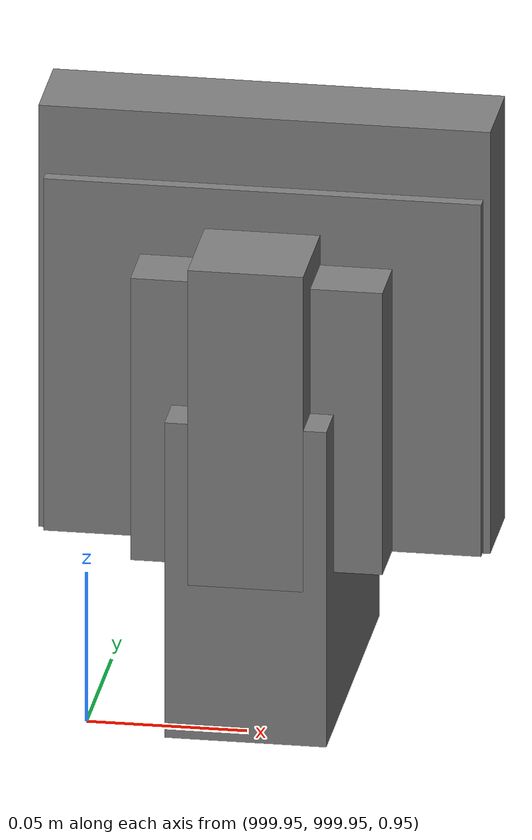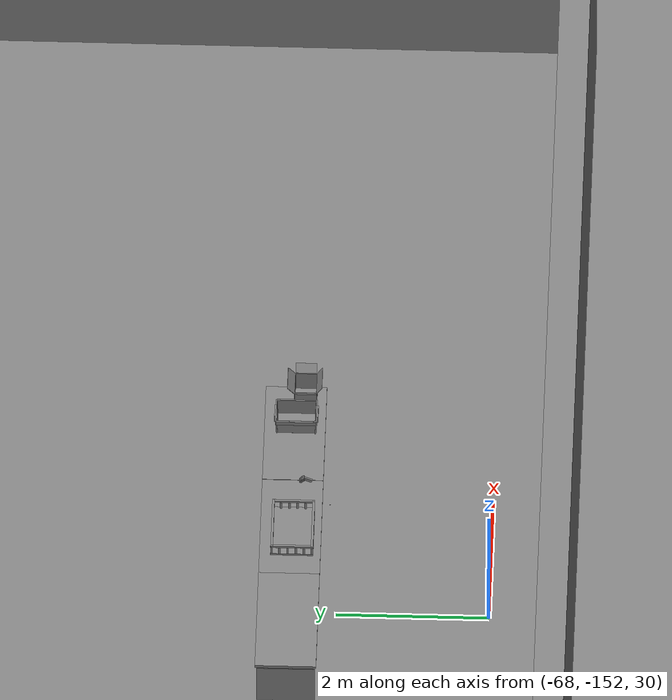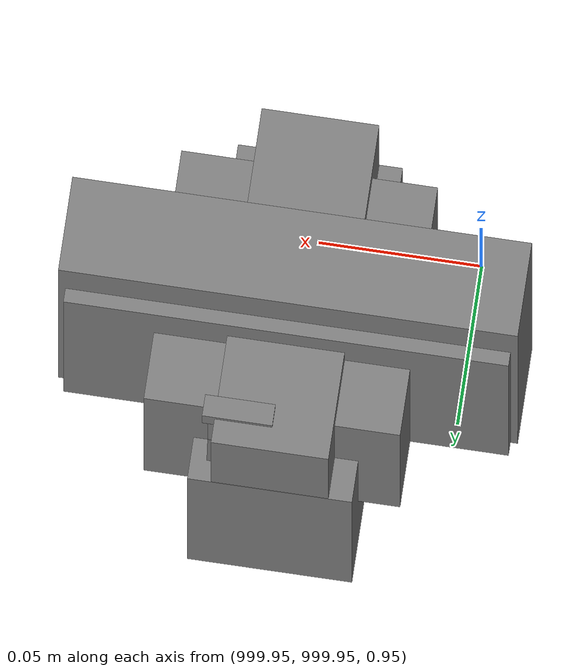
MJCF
<mujoco>
    <option gravity="0.000000000 0.000000000 -9.810000420" timestep="0.0049999999" integrator="implicitfast" density="1.225" viscosity="1.8000001e-05" noslip_iterations="10" iterations="100" sdf_iterations="50">
        <flag multiccd="disable"/>
    </option>
    <size memory="1000M"/>
    <compiler coordinate="local"/>
    <worldbody>
        <light cutoff="30" pos="0 1 1" dir="0 -1 -2"/>
        <light cutoff="30" pos="0 -1 1" dir="0 1 -2"/>
        <body pos="1000.000000000 1000.000000000 1.000000000" euler="0.000011953 0.000005123 -179.999984741" name="openloong_gripper_2f85_fix_base_usda_intel_box">
            <geom contype="1" conaffinity="1" density="1000" type="box" material="" rgba="0.500000000 0.500000000 0.500000000 1.000000000" solimp="0.899999976 0.949999988 0.001000000" friction="1.000000000 0.005000000 0.000100000" solref="0.020000000 1.000000000" margin="0" condim="3" group="0" pos="0.000000000 -0.000067139 0.000082284" quat="0.707106709 0.000000225 0.000000253 0.707106650" size="0.052800003 0.025300000 0.052800003" name="openloong_gripper_2f85_fix_base_usda_geom_87EAE7EC_9BA2_4013_AECD_D639A66352C6"/>
            <freejoint name="openloong_gripper_2f85_fix_base_usda_intel_box_joint"/>
            <site size="0.005000000 0.005000000 0.005000000" rgba="0.500000000 0.500000000 0.500000000 1.000000000" pos="0.000000000 0.000000000 0.000000000" quat="0.999961913 0.008726500 0.000000000 0.000000000" group="0" type="sphere" name="openloong_gripper_2f85_fix_base_usda_intel_boxsite"/>
        </body>
        <body pos="-66.004776001 -149.747589111 31.165941238" euler="-56.540225983 -6.860964775 171.377700806" mocap="true" name="spotlight3_SpotLight"/>
        <body pos="1000.000000000 1000.000000000 1.000000000" euler="0.000000000 0.000000000 180.000000000" name="openloong_gripper_2f85_fix_base_usda_wifi_box">
            <geom contype="1" conaffinity="1" density="1000" type="box" material="" rgba="0.500000000 0.500000000 0.500000000 1.000000000" solimp="0.899999976 0.949999988 0.001000000" friction="1.000000000 0.005000000 0.000100000" solref="0.020000000 1.000000000" margin="0" condim="3" group="0" pos="0.000000000 0.000000000 0.058978677" quat="0.000000000 0.000000047 0.000000000 1.000000000" size="0.068499997 0.018999999 0.059000000" name="openloong_gripper_2f85_fix_base_usda_geom_CCAE77A1_3CA5_4928_ACDD_39873ECB2EB2"/>
            <freejoint name="openloong_gripper_2f85_fix_base_usda_wifi_box_joint"/>
            <site size="0.005000000 0.005000000 0.005000000" rgba="0.500000000 0.500000000 0.500000000 1.000000000" pos="0.000000000 0.000000000 0.000000000" quat="0.999961913 0.008726500 0.000000000 0.000000000" group="0" type="sphere" name="openloong_gripper_2f85_fix_base_usda_wifi_boxsite"/>
        </body>
        <body pos="1000.000000000 1000.000000000 1.000000000" euler="0.000000000 0.000000000 180.000000000" name="openloong_gripper_2f85_fix_base_usda_cpu_fan">
            <geom contype="1" conaffinity="1" density="1000" type="box" material="" rgba="0.500000000 0.500000000 0.500000000 1.000000000" solimp="0.899999976 0.949999988 0.001000000" friction="1.000000000 0.005000000 0.000100000" solref="0.020000000 1.000000000" margin="0" condim="3" group="0" pos="0.000000000 0.000000000 0.070034981" quat="0.000000000 0.000000000 0.000000000 1.000000000" size="0.070700005 0.014699999 0.070700005" name="openloong_gripper_2f85_fix_base_usda_geom_887D1A32_C4AB_4DE2_B6CD_982E266C947F"/>
            <freejoint name="openloong_gripper_2f85_fix_base_usda_cpu_fan_joint"/>
            <site size="0.005000000 0.005000000 0.005000000" rgba="0.500000000 0.500000000 0.500000000 1.000000000" pos="0.000000000 0.000000000 0.000000000" quat="0.999961913 0.008726535 0.000000000 0.000000000" group="0" type="sphere" name="openloong_gripper_2f85_fix_base_usda_cpu_fancsite"/>
        </body>
        <body pos="-66.146774292 -149.045349121 31.166635513" euler="-4.011288166 78.472953796 -172.959259033" mocap="true" name="spotlight5_SpotLight"/>
        <body pos="1000.000000000 999.999938965 1.000000000" euler="0.000000000 0.000000000 180.000000000" name="openloong_gripper_2f85_fix_base_usda_intelcore_i5">
            <geom contype="1" conaffinity="1" density="1000" type="box" material="" rgba="0.500000000 0.500000000 0.500000000 1.000000000" solimp="0.899999976 0.949999988 0.001000000" friction="1.000000000 0.005000000 0.000100000" solref="0.020000000 1.000000000" margin="0" condim="3" group="0" pos="0.000000000 0.000000000 0.051722717" quat="0.707106709 0.000000000 0.000000000 -0.707106769" size="0.052800000 0.018080002 0.052800000" name="openloong_gripper_2f85_fix_base_usda_geom_92835B9D_8484_4E42_92B9_CD82AFE54FEA"/>
            <freejoint name="openloong_gripper_2f85_fix_base_usda_intelcore_i5_joint"/>
            <site size="0.005000000 0.005000000 0.005000000" rgba="0.500000000 0.500000000 0.500000000 1.000000000" pos="0.000000000 0.000000000 0.000000000" quat="0.999961913 0.008726534 0.000000000 0.000000000" group="0" type="sphere" name="openloong_gripper_2f85_fix_base_usda_intelcore_i5site"/>
        </body>
        <body pos="1000.000000000 1000.000000000 1.000000000" euler="0.000000000 0.000000000 180.000000000" name="openloong_gripper_2f85_fix_base_usda_battery_01">
            <geom contype="1" conaffinity="1" density="1000" type="box" material="" rgba="0.500000000 0.500000000 0.500000000 1.000000000" solimp="0.899999976 0.949999988 0.001000000" friction="1.000000000 0.005000000 0.000100000" solref="0.020000000 1.000000000" margin="0" condim="3" group="0" pos="-0.011123657 -0.041940309 0.101691343" quat="1.000000000 0.000000000 0.000000000 0.000000000" size="0.010800000 0.003375000 0.004725000" name="openloong_gripper_2f85_fix_base_usda_geom_83B97C6E_B874_49C5_861E_BA25B70940FC"/>
            <geom contype="1" conaffinity="1" density="1000" type="box" material="" rgba="0.500000000 0.500000000 0.500000000 1.000000000" solimp="0.899999976 0.949999988 0.001000000" friction="1.000000000 0.005000000 0.000100000" solref="0.020000000 1.000000000" margin="0" condim="3" group="0" pos="-0.010876465 -0.044247437 0.047066893" quat="0.998702705 -0.050920475 0.000000000 0.000000000" size="0.009450001 0.002700000 0.024975000" name="openloong_gripper_2f85_fix_base_usda_geom_2DC82518_BC43_4DC4_96A6_25D5B78D6572"/>
            <geom contype="1" conaffinity="1" density="1000" type="box" material="" rgba="0.500000000 0.500000000 0.500000000 1.000000000" solimp="0.899999976 0.949999988 0.001000000" friction="1.000000000 0.005000000 0.000100000" solref="0.020000000 1.000000000" margin="0" condim="3" group="0" pos="-0.001235962 -0.000659180 0.047381196" quat="1.000000000 0.000000000 0.000000000 0.000000000" size="0.039420001 0.039150000 0.047250003" name="openloong_gripper_2f85_fix_base_usda_geom_8577A846_97BA_4B1B_9F0E_691BA22CC477"/>
            <geom contype="1" conaffinity="1" density="1000" type="box" material="" rgba="0.500000000 0.500000000 0.500000000 1.000000000" solimp="0.899999976 0.949999988 0.001000000" friction="1.000000000 0.005000000 0.000100000" solref="0.020000000 1.000000000" margin="0" condim="3" group="0" pos="-0.010876465 -0.039138794 0.009851727" quat="1.000000000 0.000000000 0.000000000 0.000000000" size="0.009450001 0.010800000 0.013500000" name="openloong_gripper_2f85_fix_base_usda_geom_36E6B3E9_9B2F_4EC5_A0C9_F9CB144B181E"/>
            <geom contype="1" conaffinity="1" density="1000" type="box" material="" rgba="0.500000000 0.500000000 0.500000000 1.000000000" solimp="0.899999976 0.949999988 0.001000000" friction="1.000000000 0.005000000 0.000100000" solref="0.020000000 1.000000000" margin="0" condim="3" group="0" pos="-0.010876465 -0.041528322 0.071508206" quat="1.000000000 0.000000000 0.000000000 0.000000000" size="0.009450001 0.002700000 0.027000001" name="openloong_gripper_2f85_fix_base_usda_geom_819D1C8D_DD35_4095_A31E_89A2A18AD71C"/>
            <freejoint name="openloong_gripper_2f85_fix_base_usda_battery_01_joint"/>
            <site size="0.005000000 0.005000000 0.005000000" rgba="0.500000000 0.500000000 0.500000000 1.000000000" pos="0.000000000 0.000000000 0.000000000" quat="0.999961913 0.008726500 0.000000000 0.000000000" group="0" type="sphere" name="openloong_gripper_2f85_fix_base_usda_battery_01site"/>
        </body>
        <body pos="-65.960540771 -149.591461182 31.169002533" euler="140.450592041 -62.182586670 -156.458480835" mocap="true" name="spotlight4_SpotLight"/>
        <body pos="-64.866622925 -149.383972168 30.183746338" euler="89.999984741 89.999946594 0.000000000" name="openloong_gripper_2f85_fix_base_usda_bluebox_01">
            <geom contype="1" conaffinity="1" density="1000" type="box" material="" rgba="0.500000000 0.500000000 0.500000000 1.000000000" solimp="0.899999976 0.949999988 0.001000000" friction="1.000000000 0.005000000 0.000100000" solref="0.020000000 1.000000000" margin="0" condim="3" group="0" pos="0.276580811 0.187225342 0.000068665" quat="0.707106948 0.000077471 0.707106352 0.000077486" size="0.100000001 0.057999998 0.010000000" name="openloong_gripper_2f85_fix_base_usda_geom_C66C49E1_708A_4CBF_B75C_D92A8EB288F9"/>
            <geom contype="1" conaffinity="1" density="1000" type="box" material="" rgba="0.500000000 0.500000000 0.500000000 1.000000000" solimp="0.899999976 0.949999988 0.001000000" friction="1.000000000 0.005000000 0.000100000" solref="0.020000000 1.000000000" margin="0" condim="3" group="0" pos="0.000000000 0.002883911 0.000000000" quat="0.999999881 0.000000000 0.000000000 0.000000000" size="0.254000008 0.003000000 0.172000006" name="openloong_gripper_2f85_fix_base_usda_geom_F3E302DB_9E5C_4308_BFB3_9DEAA3D57D1D"/>
            <geom contype="1" conaffinity="1" density="1000" type="box" material="" rgba="0.500000000 0.500000000 0.500000000 1.000000000" solimp="0.899999976 0.949999988 0.001000000" friction="1.000000000 0.005000000 0.000100000" solref="0.020000000 1.000000000" margin="0" condim="3" group="0" pos="0.000000000 0.124874115 0.173484802" quat="0.999796331 0.020176515 -0.000000015 0.000000030" size="0.259999990 0.119999997 0.007000000" name="openloong_gripper_2f85_fix_base_usda_geom_77658E68_E9EB_496F_BE84_11EA2690D9FD"/>
            <geom contype="1" conaffinity="1" density="1000" type="box" material="" rgba="0.500000000 0.500000000 0.500000000 1.000000000" solimp="0.899999976 0.949999988 0.001000000" friction="1.000000000 0.005000000 0.000100000" solref="0.020000000 1.000000000" margin="0" condim="3" group="0" pos="0.000000000 0.124874115 -0.173469543" quat="0.999796331 -0.020176545 -0.000000015 0.000000000" size="0.259999990 0.119999997 0.007000000" name="openloong_gripper_2f85_fix_base_usda_geom_A7E4209D_8255_4025_AAB0_DA4D8BBBD72E"/>
            <geom contype="1" conaffinity="1" density="1000" type="box" material="" rgba="0.500000000 0.500000000 0.500000000 1.000000000" solimp="0.899999976 0.949999988 0.001000000" friction="1.000000000 0.005000000 0.000100000" solref="0.020000000 1.000000000" margin="0" condim="3" group="0" pos="0.000000000 0.214008331 0.188980103" quat="0.999912977 0.013176724 0.000000015 0.000000000" size="0.259999990 0.029999999 0.012500000" name="openloong_gripper_2f85_fix_base_usda_geom_AD2EAA1C_DC61_4EE0_AEAD_19EB27AF19FB"/>
            <geom contype="1" conaffinity="1" density="1000" type="box" material="" rgba="0.500000000 0.500000000 0.500000000 1.000000000" solimp="0.899999976 0.949999988 0.001000000" friction="1.000000000 0.005000000 0.000100000" solref="0.020000000 1.000000000" margin="0" condim="3" group="0" pos="-0.258361816 0.125289917 0.001876831" quat="0.702796936 -0.020792112 0.710783124 0.020769298" size="0.189999998 0.119999997 0.009000000" name="openloong_gripper_2f85_fix_base_usda_geom_E53EE0FA_B829_4A09_B172_7621A8C075CA"/>
            <geom contype="1" conaffinity="1" density="1000" type="box" material="" rgba="0.500000000 0.500000000 0.500000000 1.000000000" solimp="0.899999976 0.949999988 0.001000000" friction="1.000000000 0.005000000 0.000100000" solref="0.020000000 1.000000000" margin="0" condim="3" group="0" pos="0.000000000 0.214008331 -0.188980103" quat="0.999912977 -0.013176769 0.000000030 0.000000015" size="0.259999990 0.029999999 0.012500000" name="openloong_gripper_2f85_fix_base_usda_geom_75CE80E7_1FE4_4AEF_A1FE_C64850DD1011"/>
            <geom contype="1" conaffinity="1" density="1000" type="box" material="" rgba="0.500000000 0.500000000 0.500000000 1.000000000" solimp="0.899999976 0.949999988 0.001000000" friction="1.000000000 0.005000000 0.000100000" solref="0.020000000 1.000000000" margin="0" condim="3" group="0" pos="-0.276611328 0.187225342 0.000068665" quat="0.707106650 0.000077441 0.707106709 0.000077456" size="0.100000001 0.057999998 0.010000000" name="openloong_gripper_2f85_fix_base_usda_geom_0487FE5A_1C48_4349_B959_60EBFDE027A8"/>
            <geom contype="1" conaffinity="1" density="1000" type="box" material="" rgba="0.500000000 0.500000000 0.500000000 1.000000000" solimp="0.899999976 0.949999988 0.001000000" friction="1.000000000 0.005000000 0.000100000" solref="0.020000000 1.000000000" margin="0" condim="3" group="0" pos="0.258331299 0.125289917 0.001876831" quat="0.702851415 0.018856421 0.710823774 -0.019329369" size="0.189999998 0.119999997 0.009000000" name="openloong_gripper_2f85_fix_base_usda_geom_E1A6768A_DE8A_4954_A390_D5BD867B21E4"/>
            <freejoint name="openloong_gripper_2f85_fix_base_usda_bluebox_01_joint"/>
            <site size="0.005000000 0.005000000 0.005000000" rgba="0.500000000 0.500000000 0.500000000 1.000000000" pos="0.000000000 0.000000000 0.000000000" quat="0.999961913 0.008726534 0.000000000 0.000000000" group="0" type="sphere" name="openloong_gripper_2f85_fix_base_usda_bluebox_01site"/>
        </body>
        <body pos="-64.496299744 -149.491867065 30.235729218" euler="0.000000000 0.000000000 89.999946594" name="openloong_gripper_2f85_fix_base_usda_cardboardbox_01">
            <geom contype="1" conaffinity="1" density="1000" type="box" material="" rgba="0.500000000 0.500000000 0.500000000 1.000000000" solimp="0.899999976 0.949999988 0.001000000" friction="1.000000000 0.005000000 0.000100000" solref="0.020000000 1.000000000" margin="0" condim="3" group="0" pos="-0.003166199 -0.004086494 0.005052090" quat="1.000000000 0.000000000 0.000000000 0.000000000" size="0.142499998 0.177500010 0.005000000" name="openloong_gripper_2f85_fix_base_usda_geom_50559011_16E2_4A21_93C6_50B422F73CA2"/>
            <geom contype="1" conaffinity="1" density="1000" type="box" material="" rgba="0.500000000 0.500000000 0.500000000 1.000000000" solimp="0.899999976 0.949999988 0.001000000" friction="1.000000000 0.005000000 0.000100000" solref="0.020000000 1.000000000" margin="0" condim="3" group="0" pos="-0.003166199 0.170316696 0.150570869" quat="1.000000000 0.000000000 0.000000000 0.000000000" size="0.142499998 0.005000000 0.149999991" name="openloong_gripper_2f85_fix_base_usda_geom_58D18855_D117_41D7_AE52_3BB5AD2328CE"/>
            <geom contype="1" conaffinity="1" density="1000" type="box" material="" rgba="0.500000000 0.500000000 0.500000000 1.000000000" solimp="0.899999976 0.949999988 0.001000000" friction="1.000000000 0.005000000 0.000100000" solref="0.020000000 1.000000000" margin="0" condim="3" group="0" pos="-0.147399902 -0.005307198 0.150570869" quat="1.000000000 0.000000000 0.000000000 0.000000000" size="0.005000000 0.177500010 0.149999991" name="openloong_gripper_2f85_fix_base_usda_geom_366F7EE7_1C97_4680_8C1D_71340C37D5FD"/>
            <geom contype="1" conaffinity="1" density="1000" type="box" material="" rgba="0.500000000 0.500000000 0.500000000 1.000000000" solimp="0.899999976 0.949999988 0.001000000" friction="1.000000000 0.005000000 0.000100000" solref="0.020000000 1.000000000" margin="0" condim="3" group="0" pos="0.140275955 -0.005307198 0.150570869" quat="1.000000000 0.000000000 0.000000000 0.000000000" size="0.005000000 0.177500010 0.149999991" name="openloong_gripper_2f85_fix_base_usda_geom_785018AD_4C9E_4B31_A87C_14F73921E9EA"/>
            <geom contype="1" conaffinity="1" density="1000" type="box" material="" rgba="0.500000000 0.500000000 0.500000000 1.000000000" solimp="0.899999976 0.949999988 0.001000000" friction="1.000000000 0.005000000 0.000100000" solref="0.020000000 1.000000000" margin="0" condim="3" group="0" pos="-0.003166199 -0.181550980 0.150570869" quat="1.000000000 0.000000000 0.000000000 0.000000000" size="0.142499998 0.005000000 0.149999991" name="openloong_gripper_2f85_fix_base_usda_geom_E667EF5B_7839_47CC_8EB7_F830F79000DA"/>
            <freejoint name="openloong_gripper_2f85_fix_base_usda_cardboardbox_01_joint"/>
            <site size="0.005000000 0.005000000 0.005000000" rgba="0.500000000 0.500000000 0.500000000 1.000000000" pos="0.000000000 0.000000000 0.000000000" quat="0.999961913 0.008726535 0.000000000 0.000000000" group="0" type="sphere" name="openloong_gripper_2f85_fix_base_usda_site_68533145_1FBD_43F8_84A3_A82A28693E19"/>
            <body pos="0.139160156 -0.004048347 0.301930904" euler="-179.999954224 49.383502960 179.999954224" name="openloong_gripper_2f85_fix_base_usda_A1_006">
                <geom contype="1" conaffinity="1" density="1000" type="box" material="" rgba="0.500000000 0.500000000 0.500000000 1.000000000" solimp="0.899999976 0.949999988 0.001000000" friction="1.000000000 0.005000000 0.000100000" solref="0.020000000 1.000000000" margin="0" condim="3" group="0" pos="-0.071587563 0.000009537 0.001745224" quat="0.999999881 0.000000000 0.000000000 0.000000000" size="0.071249999 0.179999992 0.002500000" name="openloong_gripper_2f85_fix_base_usda_geom_D48B4AFF_5DD5_475D_9D0B_78619B9C70C2"/>
                <joint armature="0" stiffness="0.07" damping="0.0099999998" axis="0.000000 1.000000 0.000000" type="hinge" name="openloong_gripper_2f85_fix_base_usda_A1_006"/>
            </body>
            <body pos="-0.145902634 -0.004086494 0.301938057" euler="-180.000000000 -60.000011444 -180.000000000" name="openloong_gripper_2f85_fix_base_usda_A2_006">
                <geom contype="1" conaffinity="1" density="1000" type="box" material="" rgba="0.500000000 0.500000000 0.500000000 1.000000000" solimp="0.899999976 0.949999988 0.001000000" friction="1.000000000 0.005000000 0.000100000" solref="0.020000000 1.000000000" margin="0" condim="3" group="0" pos="0.071268082 0.000009537 0.002717972" quat="0.000002921 0.000000000 -0.000000030 0.999999881" size="0.071249999 0.179999992 0.002500000" name="openloong_gripper_2f85_fix_base_usda_geom_FC37DC7E_70F3_4BDF_917B_E67918428EE1"/>
                <joint armature="0" stiffness="0.07" damping="0.0099999998" axis="0.000000 1.000000 0.000000" type="hinge" name="openloong_gripper_2f85_fix_base_usda_A2_006"/>
            </body>
            <body pos="-0.003385544 0.175991058 0.301930904" euler="-125.858116150 -0.000004561 0.000002331" name="openloong_gripper_2f85_fix_base_usda_B2_006">
                <geom contype="1" conaffinity="1" density="1000" type="box" material="" rgba="0.500000000 0.500000000 0.500000000 1.000000000" solimp="0.899999976 0.949999988 0.001000000" friction="1.000000000 0.005000000 0.000100000" solref="0.020000000 1.000000000" margin="0" condim="3" group="0" pos="0.000009537 -0.070939064 -0.002470016" quat="0.999614120 0.027776197 -0.000000015 0.000000030" size="0.137500003 0.064999998 0.005000000" name="openloong_gripper_2f85_fix_base_usda_geom_1CAA37D4_7AEE_417B_88D9_6BF70D90F7D8"/>
                <joint armature="0" stiffness="0.07" damping="0.0099999998" axis="1.000000 0.000000 0.000000" type="hinge" name="openloong_gripper_2f85_fix_base_usda_B2_006"/>
            </body>
            <body pos="-0.003385544 -0.184140205 0.301938057" euler="147.805557251 0.000000000 0.000000000" name="openloong_gripper_2f85_fix_base_usda_B1_006">
                <geom contype="1" conaffinity="1" density="1000" type="box" material="" rgba="0.500000000 0.500000000 0.500000000 1.000000000" solimp="0.899999976 0.949999988 0.001000000" friction="1.000000000 0.005000000 0.000100000" solref="0.020000000 1.000000000" margin="0" condim="3" group="0" pos="-0.000028610 0.070202351 -0.002703667" quat="0.999614179 -0.027776167 0.000000000 0.000000000" size="0.137500003 0.064999998 0.005000000" name="openloong_gripper_2f85_fix_base_usda_geom_855642D1_D0D5_41E1_93BE_6630AD6298E4"/>
                <joint armature="0" stiffness="0.07" damping="0.0099999998" axis="1.000000 0.000000 0.000000" type="hinge" name="openloong_gripper_2f85_fix_base_usda_B1_006"/>
            </body>
        </body>
        <body pos="-65.882858276 -149.481979370 30.229999542" euler="-64.487716675 0.000000000 0.000000000" name="openloong_gripper_2f85_fix_base_usda_Barcode">
            <geom contype="1" conaffinity="1" density="1000" type="box" material="" rgba="0.500000000 0.500000000 0.500000000 1.000000000" solimp="0.899999976 0.949999988 0.001000000" friction="1.000000000 0.005000000 0.000100000" solref="0.020000000 1.000000000" margin="0" condim="3" group="0" pos="0.000000000 0.013038635 0.001419067" quat="0.000000000 0.000000000 0.000000000 1.000000119" size="0.034000002 0.010000000 0.017999999" name="openloong_gripper_2f85_fix_base_usda_geom_BFF0491F_AABE_4126_A0DD_E57B1A8EC95F"/>
            <geom contype="1" conaffinity="1" density="1000" type="box" material="" rgba="0.500000000 0.500000000 0.500000000 1.000000000" solimp="0.899999976 0.949999988 0.001000000" friction="1.000000000 0.005000000 0.000100000" solref="0.020000000 1.000000000" margin="0" condim="3" group="0" pos="0.000000000 -0.035301208 -0.007095337" quat="0.000000000 0.000000000 -0.043619365 0.999048233" size="0.028999999 0.010000000 0.020000000" name="openloong_gripper_2f85_fix_base_usda_geom_FF29AFFB_7A94_4333_9FA8_AA4F0FE1C0B8"/>
            <geom contype="1" conaffinity="1" density="1000" type="box" material="" rgba="0.500000000 0.500000000 0.500000000 1.000000000" solimp="0.899999976 0.949999988 0.001000000" friction="1.000000000 0.005000000 0.000100000" solref="0.020000000 1.000000000" margin="0" condim="3" group="0" pos="0.000000000 -0.043411255 -0.011749268" quat="0.922262907 0.386563420 0.000000000 0.000000000" size="0.026000001 0.010000000 0.020000000" name="openloong_gripper_2f85_fix_base_usda_geom_7389F53D_CAF2_4341_A7E4_D7F9FDCC1380"/>
            <geom contype="1" conaffinity="1" density="1000" type="box" material="" rgba="0.500000000 0.500000000 0.500000000 1.000000000" solimp="0.899999976 0.949999988 0.001000000" friction="1.000000000 0.005000000 0.000100000" solref="0.020000000 1.000000000" margin="0" condim="3" group="0" pos="0.000000000 -0.016967773 -0.031860352" quat="0.000000000 0.000000000 0.000000000 1.000000119" size="0.008000000 0.010000000 0.013000000" name="openloong_gripper_2f85_fix_base_usda_geom_7565C9C0_FC8F_427C_B32E_2A2167726A81"/>
            <geom contype="1" conaffinity="1" density="1000" type="box" material="" rgba="0.500000000 0.500000000 0.500000000 1.000000000" solimp="0.899999976 0.949999988 0.001000000" friction="1.000000000 0.005000000 0.000100000" solref="0.020000000 1.000000000" margin="0" condim="3" group="0" pos="0.000000000 -0.001869202 0.000312805" quat="0.953716993 0.300705761 0.000000000 0.000000000" size="0.032000002 0.010000000 0.018999999" name="openloong_gripper_2f85_fix_base_usda_geom_D05C1378_0BC9_46B3_943F_8E0E7B705A76"/>
            <geom contype="1" conaffinity="1" density="1000" type="box" material="" rgba="0.500000000 0.500000000 0.500000000 1.000000000" solimp="0.899999976 0.949999988 0.001000000" friction="1.000000000 0.005000000 0.000100000" solref="0.020000000 1.000000000" margin="0" condim="3" group="0" pos="0.000000000 -0.019531250 -0.003173828" quat="0.953716993 0.300705761 0.000000000 0.000000000" size="0.030999999 0.010000000 0.020000000" name="openloong_gripper_2f85_fix_base_usda_geom_5FF92C35_478F_4B76_AF82_29B6BAF6449C"/>
            <geom contype="1" conaffinity="1" density="1000" type="box" material="" rgba="0.500000000 0.500000000 0.500000000 1.000000000" solimp="0.899999976 0.949999988 0.001000000" friction="1.000000000 0.005000000 0.000100000" solref="0.020000000 1.000000000" margin="0" condim="3" group="0" pos="0.000000000 -0.035301208 -0.007095337" quat="0.953716993 0.300705761 0.000000000 0.000000000" size="0.028999999 0.010000000 0.020000000" name="openloong_gripper_2f85_fix_base_usda_geom_C3F4746A_EEA4_4D82_9D71_D9520ED2FC48"/>
            <geom contype="1" conaffinity="1" density="1000" type="box" material="" rgba="0.500000000 0.500000000 0.500000000 1.000000000" solimp="0.899999976 0.949999988 0.001000000" friction="1.000000000 0.005000000 0.000100000" solref="0.020000000 1.000000000" margin="0" condim="3" group="0" pos="0.000000000 -0.042617798 -0.071121216" quat="0.000000000 0.000000000 0.000000000 1.000000119" size="0.013000000 0.021000000 0.059999999" name="openloong_gripper_2f85_fix_base_usda_geom_C7475E9A_AF74_4A65_A3BE_B50343F6D923"/>
            <freejoint name="openloong_gripper_2f85_fix_base_usda_Barcode_joint"/>
            <site size="0.005000000 0.005000000 0.005000000" rgba="0.500000000 0.500000000 0.500000000 1.000000000" pos="0.000000000 0.000000000 0.000000000" quat="1.000000000 0.000000000 0.000000000 0.000000000" group="0" type="sphere" name="openloong_gripper_2f85_fix_base_usda_Barcode_site"/>
        </body>
        <body pos="-66.745018005 -149.392349243 30.184000015" euler="0.000000000 0.000000000 89.999946594" name="[22333714075314]_Basket_01">
            <geom contype="1" conaffinity="1" density="1000" type="box" material="" rgba="0.500000000 0.500000000 0.500000000 1.000000000" solimp="0.899999976 0.949999988 0.001000000" friction="1.000000000 0.005000000 0.000100000" solref="0.020000000 1.000000000" margin="0" condim="3" group="0" pos="-0.052425385 0.389207840 0.089787483" quat="0.707107008 0.000000000 0.000000000 0.707106411" size="0.014249999 0.014249999 0.059999999" name="[22333714075314]_geom_A91ADBE5_E65E_45BA_ABB0_A57911F50401"/>
            <geom contype="1" conaffinity="1" density="1000" type="box" material="" rgba="0.500000000 0.500000000 0.500000000 1.000000000" solimp="0.899999976 0.949999988 0.001000000" friction="1.000000000 0.005000000 0.000100000" solref="0.020000000 1.000000000" margin="0" condim="3" group="0" pos="0.264015198 -0.133043289 0.089787483" quat="0.707107008 0.000000000 0.000000000 0.707106411" size="0.014249999 0.014249999 0.059999999" name="[22333714075314]_geom_8D383431_EA40_4AA3_BAE0_88FCE7EA65D0"/>
            <geom contype="1" conaffinity="1" density="1000" type="box" material="" rgba="0.500000000 0.500000000 0.500000000 1.000000000" solimp="0.899999976 0.949999988 0.001000000" friction="1.000000000 0.005000000 0.000100000" solref="0.020000000 1.000000000" margin="0" condim="3" group="0" pos="-0.264015198 -0.265548706 0.089793205" quat="0.707107008 0.000000000 0.000000000 0.707106411" size="0.014249999 0.014249999 0.059999999" name="[22333714075314]_geom_EC28A585_BB98_4F2A_8DCD_9DA19909CAA7"/>
            <geom contype="1" conaffinity="1" density="1000" type="box" material="" rgba="0.500000000 0.500000000 0.500000000 1.000000000" solimp="0.899999976 0.949999988 0.001000000" friction="1.000000000 0.005000000 0.000100000" solref="0.020000000 1.000000000" margin="0" condim="3" group="0" pos="-0.160263062 -0.389322281 0.089793205" quat="0.707107008 0.000000000 0.000000000 0.707106411" size="0.014249999 0.014249999 0.059999999" name="[22333714075314]_geom_4DFCFA99_802E_4D51_A405_B8C25A579363"/>
            <geom contype="1" conaffinity="1" density="1000" type="box" material="" rgba="0.500000000 0.500000000 0.500000000 1.000000000" solimp="0.899999976 0.949999988 0.001000000" friction="1.000000000 0.005000000 0.000100000" solref="0.020000000 1.000000000" margin="0" condim="3" group="0" pos="0.162265778 -0.389322281 0.089787483" quat="0.707107008 0.000000000 0.000000000 0.707106411" size="0.014249999 0.014249999 0.059999999" name="[22333714075314]_geom_990E8F81_56AE_4210_B96F_824FAAF10C36"/>
            <geom contype="1" conaffinity="1" density="1000" type="box" material="" rgba="0.500000000 0.500000000 0.500000000 1.000000000" solimp="0.899999976 0.949999988 0.001000000" friction="1.000000000 0.005000000 0.000100000" solref="0.020000000 1.000000000" margin="0" condim="3" group="0" pos="0.264015198 0.389207840 0.089787483" quat="0.707107008 0.000000000 0.000000000 0.707106411" size="0.014249999 0.014249999 0.059999999" name="[22333714075314]_geom_D6DD0A22_9389_4E61_9365_52FCFAA83E38"/>
            <geom contype="1" conaffinity="1" density="1000" type="box" material="" rgba="0.500000000 0.500000000 0.500000000 1.000000000" solimp="0.899999976 0.949999988 0.001000000" friction="1.000000000 0.005000000 0.000100000" solref="0.020000000 1.000000000" margin="0" condim="3" group="0" pos="-0.264015198 -0.133043289 0.089793205" quat="0.707107008 0.000000000 0.000000000 0.707106411" size="0.014249999 0.014249999 0.059999999" name="[22333714075314]_geom_D7D9523D_13DF_4983_AF82_7C4677A86D13"/>
            <geom contype="1" conaffinity="1" density="1000" type="box" material="" rgba="0.500000000 0.500000000 0.500000000 1.000000000" solimp="0.899999976 0.949999988 0.001000000" friction="1.000000000 0.005000000 0.000100000" solref="0.020000000 1.000000000" margin="0" condim="3" group="0" pos="-0.264026642 0.269256592 0.089793205" quat="0.707107008 0.000000000 0.000000000 0.707106411" size="0.014249999 0.014249999 0.059999999" name="[22333714075314]_geom_3BD9CF52_F239_4912_89B0_DA59701F70E2"/>
            <geom contype="1" conaffinity="1" density="1000" type="box" material="" rgba="0.500000000 0.500000000 0.500000000 1.000000000" solimp="0.899999976 0.949999988 0.001000000" friction="1.000000000 0.005000000 0.000100000" solref="0.020000000 1.000000000" margin="0" condim="3" group="0" pos="0.054462433 0.389207840 0.089787483" quat="0.707107008 0.000000000 0.000000000 0.707106411" size="0.014249999 0.014249999 0.059999999" name="[22333714075314]_geom_6EB2670B_4B43_417C_B97D_26721D176B4A"/>
            <geom contype="1" conaffinity="1" density="1000" type="box" material="" rgba="0.500000000 0.500000000 0.500000000 1.000000000" solimp="0.899999976 0.949999988 0.001000000" friction="1.000000000 0.005000000 0.000100000" solref="0.020000000 1.000000000" margin="0" condim="3" group="0" pos="0.054462433 -0.389322281 0.089787483" quat="0.707107008 0.000000000 0.000000000 0.707106411" size="0.014249999 0.014249999 0.059999999" name="[22333714075314]_geom_E887B4FB_4254_46E8_A339_998E0DDDF89D"/>
            <geom contype="1" conaffinity="1" density="1000" type="box" material="" rgba="0.500000000 0.500000000 0.500000000 1.000000000" solimp="0.899999976 0.949999988 0.001000000" friction="1.000000000 0.005000000 0.000100000" solref="0.020000000 1.000000000" margin="0" condim="3" group="0" pos="0.264015198 0.269256592 0.089793205" quat="0.707107008 0.000000000 0.000000000 0.707106411" size="0.014249999 0.014249999 0.059999999" name="[22333714075314]_geom_2639A184_8624_42F4_8E73_D7C1BF9D4373"/>
            <geom contype="1" conaffinity="1" density="1000" type="box" material="" rgba="0.500000000 0.500000000 0.500000000 1.000000000" solimp="0.899999976 0.949999988 0.001000000" friction="1.000000000 0.005000000 0.000100000" solref="0.020000000 1.000000000" margin="0" condim="3" group="0" pos="0.264015198 -0.389322281 0.089787483" quat="0.707107008 0.000000000 0.000000000 0.707106411" size="0.014249999 0.014249999 0.059999999" name="[22333714075314]_geom_306634D8_4F50_4256_97BD_B38A9C83CE59"/>
            <geom contype="1" conaffinity="1" density="1000" type="box" material="" rgba="0.500000000 0.500000000 0.500000000 1.000000000" solimp="0.899999976 0.949999988 0.001000000" friction="1.000000000 0.005000000 0.000100000" solref="0.020000000 1.000000000" margin="0" condim="3" group="0" pos="0.000000000 0.000000000 0.015998840" quat="0.707107008 0.000000000 0.000000000 0.707106411" size="0.403499991 0.279000014 0.015750000" name="[22333714075314]_geom_759C9EDB_76D4_4A40_A998_78B85AC61536"/>
            <geom contype="1" conaffinity="1" density="1000" type="box" material="" rgba="0.500000000 0.500000000 0.500000000 1.000000000" solimp="0.899999976 0.949999988 0.001000000" friction="1.000000000 0.005000000 0.000100000" solref="0.020000000 1.000000000" margin="0" condim="3" group="0" pos="0.000000000 -0.389476776 0.163619041" quat="0.707107008 0.000000000 0.000000000 0.707106411" size="0.015000000 0.277500004 0.015750000" name="[22333714075314]_geom_BE728C91_9B88_484A_8E1C_F2C19D46E830"/>
            <geom contype="1" conaffinity="1" density="1000" type="box" material="" rgba="0.500000000 0.500000000 0.500000000 1.000000000" solimp="0.899999976 0.949999988 0.001000000" friction="1.000000000 0.005000000 0.000100000" solref="0.020000000 1.000000000" margin="0" condim="3" group="0" pos="0.162265778 0.389207840 0.089787483" quat="0.707107008 0.000000000 0.000000000 0.707106411" size="0.014249999 0.014249999 0.059999999" name="[22333714075314]_geom_2DC8BED0_EE6C_497C_85BE_2205D3774EF8"/>
            <geom contype="1" conaffinity="1" density="1000" type="box" material="" rgba="0.500000000 0.500000000 0.500000000 1.000000000" solimp="0.899999976 0.949999988 0.001000000" friction="1.000000000 0.005000000 0.000100000" solref="0.020000000 1.000000000" margin="0" condim="3" group="0" pos="0.000000000 0.389471054 0.163619041" quat="0.707107008 0.000000000 0.000000000 0.707106411" size="0.015000000 0.277500004 0.015750000" name="[22333714075314]_geom_DB9633D2_BFE3_4BE3_A0E0_F4246591F957"/>
            <geom contype="1" conaffinity="1" density="1000" type="box" material="" rgba="0.500000000 0.500000000 0.500000000 1.000000000" solimp="0.899999976 0.949999988 0.001000000" friction="1.000000000 0.005000000 0.000100000" solref="0.020000000 1.000000000" margin="0" condim="3" group="0" pos="-0.263511658 0.000000000 0.163619041" quat="0.707107008 0.000000000 0.000000000 0.707106411" size="0.403499991 0.015000000 0.015750000" name="[22333714075314]_geom_AF601C05_98E7_425C_817A_BA359B19499E"/>
            <geom contype="1" conaffinity="1" density="1000" type="box" material="" rgba="0.500000000 0.500000000 0.500000000 1.000000000" solimp="0.899999976 0.949999988 0.001000000" friction="1.000000000 0.005000000 0.000100000" solref="0.020000000 1.000000000" margin="0" condim="3" group="0" pos="-0.264015198 0.141334534 0.089793205" quat="0.707107008 0.000000000 0.000000000 0.707106411" size="0.014249999 0.014249999 0.059999999" name="[22333714075314]_geom_7C2C36FA_EA3C_4797_BCF0_DE1B3EF72B27"/>
            <geom contype="1" conaffinity="1" density="1000" type="box" material="" rgba="0.500000000 0.500000000 0.500000000 1.000000000" solimp="0.899999976 0.949999988 0.001000000" friction="1.000000000 0.005000000 0.000100000" solref="0.020000000 1.000000000" margin="0" condim="3" group="0" pos="0.264015198 -0.265548706 0.089787483" quat="0.707107008 0.000000000 0.000000000 0.707106411" size="0.014249999 0.014249999 0.059999999" name="[22333714075314]_geom_3D0A4CD7_1948_4B08_AF74_7CD81C1E6138"/>
            <geom contype="1" conaffinity="1" density="1000" type="box" material="" rgba="0.500000000 0.500000000 0.500000000 1.000000000" solimp="0.899999976 0.949999988 0.001000000" friction="1.000000000 0.005000000 0.000100000" solref="0.020000000 1.000000000" margin="0" condim="3" group="0" pos="-0.160263062 0.389207840 0.089787483" quat="0.707107008 0.000000000 0.000000000 0.707106411" size="0.014249999 0.014249999 0.059999999" name="[22333714075314]_geom_05102FB3_2FED_47AE_AC5D_F9C5A22444AD"/>
            <geom contype="1" conaffinity="1" density="1000" type="box" material="" rgba="0.500000000 0.500000000 0.500000000 1.000000000" solimp="0.899999976 0.949999988 0.001000000" friction="1.000000000 0.005000000 0.000100000" solref="0.020000000 1.000000000" margin="0" condim="3" group="0" pos="-0.052425385 -0.389322281 0.089787483" quat="0.707107008 0.000000000 0.000000000 0.707106411" size="0.014249999 0.014249999 0.059999999" name="[22333714075314]_geom_A5564954_C56A_444C_BB15_71F9B630E64B"/>
            <geom contype="1" conaffinity="1" density="1000" type="box" material="" rgba="0.500000000 0.500000000 0.500000000 1.000000000" solimp="0.899999976 0.949999988 0.001000000" friction="1.000000000 0.005000000 0.000100000" solref="0.020000000 1.000000000" margin="0" condim="3" group="0" pos="-0.264026642 -0.389322281 0.089793205" quat="0.707107008 0.000000000 0.000000000 0.707106411" size="0.014249999 0.014249999 0.059999999" name="[22333714075314]_geom_CE76D17A_5224_4FF1_8398_1B859389A069"/>
            <geom contype="1" conaffinity="1" density="1000" type="box" material="" rgba="0.500000000 0.500000000 0.500000000 1.000000000" solimp="0.899999976 0.949999988 0.001000000" friction="1.000000000 0.005000000 0.000100000" solref="0.020000000 1.000000000" margin="0" condim="3" group="0" pos="0.264015198 0.141334534 0.089787483" quat="0.707107008 0.000000000 0.000000000 0.707106411" size="0.014249999 0.014249999 0.059999999" name="[22333714075314]_geom_C5A00638_3671_4235_89A0_3825CD3966C9"/>
            <geom contype="1" conaffinity="1" density="1000" type="box" material="" rgba="0.500000000 0.500000000 0.500000000 1.000000000" solimp="0.899999976 0.949999988 0.001000000" friction="1.000000000 0.005000000 0.000100000" solref="0.020000000 1.000000000" margin="0" condim="3" group="0" pos="-0.264015198 0.389207840 0.089793205" quat="0.707107008 0.000000000 0.000000000 0.707106411" size="0.014249999 0.014249999 0.059999999" name="[22333714075314]_geom_F932A160_91DD_4172_B79A_64ABF5EB6CDE"/>
            <geom contype="1" conaffinity="1" density="1000" type="box" material="" rgba="0.500000000 0.500000000 0.500000000 1.000000000" solimp="0.899999976 0.949999988 0.001000000" friction="1.000000000 0.005000000 0.000100000" solref="0.020000000 1.000000000" margin="0" condim="3" group="0" pos="0.264015198 0.004480362 0.089787483" quat="0.707107008 0.000000000 0.000000000 0.707106411" size="0.014249999 0.014249999 0.059999999" name="[22333714075314]_geom_DE54249D_107F_4E71_9FA2_32416176F36E"/>
            <geom contype="1" conaffinity="1" density="1000" type="box" material="" rgba="0.500000000 0.500000000 0.500000000 1.000000000" solimp="0.899999976 0.949999988 0.001000000" friction="1.000000000 0.005000000 0.000100000" solref="0.020000000 1.000000000" margin="0" condim="3" group="0" pos="0.263694763 -0.000011444 0.163619041" quat="0.707107008 0.000000000 0.000000000 0.707106411" size="0.403499991 0.015000000 0.015750000" name="[22333714075314]_geom_5EDA147D_71F5_47CC_9646_E6B1FE3D7329"/>
            <geom contype="1" conaffinity="1" density="1000" type="box" material="" rgba="0.500000000 0.500000000 0.500000000 1.000000000" solimp="0.899999976 0.949999988 0.001000000" friction="1.000000000 0.005000000 0.000100000" solref="0.020000000 1.000000000" margin="0" condim="3" group="0" pos="-0.264015198 0.004480362 0.089793205" quat="0.707107008 0.000000000 0.000000000 0.707106411" size="0.014249999 0.014249999 0.059999999" name="[22333714075314]_geom_744F967B_4AF7_4465_825C_968E7F618ECC"/>
            <freejoint name="[22333714075314]_joint_4882D541_E503_4706_8BF2_18E1B4D55044"/>
        </body>
        <body pos="0.000000000 0.000000000 0.000000000" euler="0.000000000 0.000000000 0.000000000" name="Static Objects_Static Objects">
            <geom contype="1" conaffinity="1" density="1000" type="box" material="" rgba="0.500000000 0.500000000 0.500000000 1.000000000" solimp="0.899999976 0.949999988 0.001000000" friction="1.000000000 0.005000000 0.000100000" solref="0.020000000 1.000000000" margin="0" condim="3" group="0" pos="-67.544113159 -149.365814209 29.727830887" quat="0.500000417 0.499999970 0.499999553 0.499999970" size="0.381000012 0.319999993 0.041000001" name="Static Objects_geom_FB8A8095_153C_4462_ADB9_6FA23EAE2146"/>
            <geom contype="1" conaffinity="1" density="1000" type="box" material="" rgba="0.500000000 0.500000000 0.500000000 1.000000000" solimp="0.899999976 0.949999988 0.001000000" friction="1.000000000 0.005000000 0.000100000" solref="0.020000000 1.000000000" margin="0" condim="3" group="0" pos="-68.239501953 -149.365814209 30.086868286" quat="0.500000417 0.499999970 0.499999553 0.499999970" size="0.370999992 0.039500002 0.745000005" name="Static Objects_geom_195D071D_3680_4FCF_8DC6_357E92849A35"/>
            <geom contype="1" conaffinity="1" density="1000" type="box" material="" rgba="0.500000000 0.500000000 0.500000000 1.000000000" solimp="0.899999976 0.949999988 0.001000000" friction="1.000000000 0.005000000 0.000100000" solref="0.020000000 1.000000000" margin="0" condim="3" group="0" pos="-68.239501953 -149.365814209 30.147235870" quat="0.500000417 0.499999970 0.499999553 0.499999970" size="0.400000006 0.022000000 0.800000012" name="Static Objects_geom_BBE8C031_CAB4_429B_B53B_C9CC209D7A05"/>
            <geom contype="1" conaffinity="1" density="1000" type="box" material="" rgba="0.500000000 0.500000000 0.500000000 1.000000000" solimp="0.899999976 0.949999988 0.001000000" friction="1.000000000 0.005000000 0.000100000" solref="0.020000000 1.000000000" margin="0" condim="3" group="0" pos="-68.934890747 -149.365814209 29.727830887" quat="0.500000417 0.499999970 0.499999553 0.499999970" size="0.381000012 0.319999993 0.041000001" name="Static Objects_geom_0DE15C23_DC88_49C4_8599_7646265AF23A"/>
            <geom contype="1" conaffinity="1" density="1000" type="box" material="" rgba="0.500000000 0.500000000 0.500000000 1.000000000" solimp="0.899999976 0.949999988 0.001000000" friction="1.000000000 0.005000000 0.000100000" solref="0.020000000 1.000000000" margin="0" condim="3" group="0" pos="-68.239501953 -149.365814209 29.561563492" quat="0.500000417 0.499999970 0.499999553 0.499999970" size="0.020000000 0.022000000 0.660000026" name="Static Objects_geom_E8963AFD_C7DE_47EB_B566_C79CD600AF4C"/>
            <geom contype="1" conaffinity="1" density="1000" type="box" material="" rgba="0.500000000 0.500000000 0.500000000 1.000000000" solimp="0.899999976 0.949999988 0.001000000" friction="1.000000000 0.005000000 0.000100000" solref="0.020000000 1.000000000" margin="0" condim="3" group="0" pos="-65.945671082 -149.365814209 29.727830887" quat="0.500000417 0.499999970 0.499999553 0.499999970" size="0.381000012 0.319999993 0.041000001" name="Static Objects_geom_D2DD1092_F4BB_40C6_9E1E_CFD19A80F71E"/>
            <geom contype="1" conaffinity="1" density="1000" type="box" material="" rgba="0.500000000 0.500000000 0.500000000 1.000000000" solimp="0.899999976 0.949999988 0.001000000" friction="1.000000000 0.005000000 0.000100000" solref="0.020000000 1.000000000" margin="0" condim="3" group="0" pos="-66.641059875 -149.365814209 30.086868286" quat="0.500000417 0.499999970 0.499999553 0.499999970" size="0.370999992 0.039500002 0.745000005" name="Static Objects_geom_3F245C47_C3A2_4268_BABE_A7538C927BE8"/>
            <geom contype="1" conaffinity="1" density="1000" type="box" material="" rgba="0.500000000 0.500000000 0.500000000 1.000000000" solimp="0.899999976 0.949999988 0.001000000" friction="1.000000000 0.005000000 0.000100000" solref="0.020000000 1.000000000" margin="0" condim="3" group="0" pos="-66.641059875 -149.365814209 30.147235870" quat="0.500000417 0.499999970 0.499999553 0.499999970" size="0.400000006 0.022000000 0.800000012" name="Static Objects_geom_5865A069_B816_44D9_A911_3600C1AE7D01"/>
            <geom contype="1" conaffinity="1" density="1000" type="box" material="" rgba="0.500000000 0.500000000 0.500000000 1.000000000" solimp="0.899999976 0.949999988 0.001000000" friction="1.000000000 0.005000000 0.000100000" solref="0.020000000 1.000000000" margin="0" condim="3" group="0" pos="-67.336448669 -149.365814209 29.727830887" quat="0.500000417 0.499999970 0.499999553 0.499999970" size="0.381000012 0.319999993 0.041000001" name="Static Objects_geom_9994AD0C_4A78_4A7F_8C98_50E667DDFE70"/>
            <geom contype="1" conaffinity="1" density="1000" type="box" material="" rgba="0.500000000 0.500000000 0.500000000 1.000000000" solimp="0.899999976 0.949999988 0.001000000" friction="1.000000000 0.005000000 0.000100000" solref="0.020000000 1.000000000" margin="0" condim="3" group="0" pos="-66.641059875 -149.365814209 29.561563492" quat="0.500000417 0.499999970 0.499999553 0.499999970" size="0.020000000 0.022000000 0.660000026" name="Static Objects_geom_1DB92C93_7B39_4ED0_ACB7_E560E5E7D642"/>
            <geom contype="1" conaffinity="1" density="1000" type="box" material="" rgba="0.500000000 0.500000000 0.500000000 1.000000000" solimp="0.899999976 0.949999988 0.001000000" friction="1.000000000 0.005000000 0.000100000" solref="0.020000000 1.000000000" margin="0" condim="3" group="0" pos="-64.338577271 -149.365814209 29.727830887" quat="0.500000417 0.499999970 0.499999553 0.499999970" size="0.381000012 0.319999993 0.041000001" name="Static Objects_geom_C306D0A6_7DD2_43B9_A498_F7FFBD616C66"/>
            <geom contype="1" conaffinity="1" density="1000" type="box" material="" rgba="0.500000000 0.500000000 0.500000000 1.000000000" solimp="0.899999976 0.949999988 0.001000000" friction="1.000000000 0.005000000 0.000100000" solref="0.020000000 1.000000000" margin="0" condim="3" group="0" pos="-65.033966064 -149.365814209 30.086868286" quat="0.500000417 0.499999970 0.499999553 0.499999970" size="0.370999992 0.039500002 0.745000005" name="Static Objects_geom_D4C0C57F_9A54_40ED_B1A6_80F9214B6380"/>
            <geom contype="1" conaffinity="1" density="1000" type="box" material="" rgba="0.500000000 0.500000000 0.500000000 1.000000000" solimp="0.899999976 0.949999988 0.001000000" friction="1.000000000 0.005000000 0.000100000" solref="0.020000000 1.000000000" margin="0" condim="3" group="0" pos="-65.033966064 -149.365814209 30.147235870" quat="0.500000417 0.499999970 0.499999553 0.499999970" size="0.400000006 0.022000000 0.800000012" name="Static Objects_geom_ACC66B8E_DF3D_4898_A7BB_AD368FD02FEC"/>
            <geom contype="1" conaffinity="1" density="1000" type="box" material="" rgba="0.500000000 0.500000000 0.500000000 1.000000000" solimp="0.899999976 0.949999988 0.001000000" friction="1.000000000 0.005000000 0.000100000" solref="0.020000000 1.000000000" margin="0" condim="3" group="0" pos="-65.729354858 -149.365814209 29.727830887" quat="0.500000417 0.499999970 0.499999553 0.499999970" size="0.381000012 0.319999993 0.041000001" name="Static Objects_geom_763AFCC8_1999_41AD_A9E8_D76EDF2C41F2"/>
            <geom contype="1" conaffinity="1" density="1000" type="box" material="" rgba="0.500000000 0.500000000 0.500000000 1.000000000" solimp="0.899999976 0.949999988 0.001000000" friction="1.000000000 0.005000000 0.000100000" solref="0.020000000 1.000000000" margin="0" condim="3" group="0" pos="-65.033966064 -149.365814209 29.561563492" quat="0.500000417 0.499999970 0.499999553 0.499999970" size="0.020000000 0.022000000 0.660000026" name="Static Objects_geom_3D81DF5D_40B2_4024_963E_0BFCC6F661E4"/>
            <geom contype="1" conaffinity="1" density="1000" type="box" material="" rgba="0.500000000 0.500000000 0.500000000 1.000000000" solimp="0.899999976 0.949999988 0.001000000" friction="1.000000000 0.005000000 0.000100000" solref="0.020000000 1.000000000" margin="0" condim="3" group="0" pos="-61.754566193 -137.853729248 33.906845093" quat="0.707107067 0.000000000 0.000000000 0.707106471" size="0.759999990 0.759999990 4.500000000" name="Static Objects_geom_5DAD8786_5EBC_446C_B164_5CBA988CBCF5"/>
            <geom contype="1" conaffinity="1" density="1000" type="box" material="" rgba="0.500000000 0.500000000 0.500000000 1.000000000" solimp="0.899999976 0.949999988 0.001000000" friction="1.000000000 0.005000000 0.000100000" solref="0.020000000 1.000000000" margin="0" condim="3" group="0" pos="-57.511135101 -144.927108765 31.707921982" quat="1.000000000 0.000000000 0.000000000 0.000000000" size="0.200000003 8.000000000 2.299999952" name="Static Objects_geom_105165D0_A95D_445A_B793_0509C72C1709"/>
            <geom contype="1" conaffinity="1" density="1000" type="box" material="" rgba="0.500000000 0.500000000 0.500000000 1.000000000" solimp="0.899999976 0.949999988 0.001000000" friction="1.000000000 0.005000000 0.000100000" solref="0.020000000 1.000000000" margin="0" condim="3" group="0" pos="-80.517646790 -157.574050903 31.688196182" quat="0.707107067 0.000000000 0.000000000 0.707106471" size="0.600000024 0.600000024 2.299999952" name="Static Objects_geom_9110620D_DED8_47CA_93DB_E5FB1751792A"/>
            <geom contype="1" conaffinity="1" density="1000" type="box" material="" rgba="0.500000000 0.500000000 0.500000000 1.000000000" solimp="0.899999976 0.949999988 0.001000000" friction="1.000000000 0.005000000 0.000100000" solref="0.020000000 1.000000000" margin="0" condim="3" group="0" pos="-80.711044312 -147.414932251 31.666158676" quat="1.000000000 0.000000000 0.000000000 0.000000000" size="0.200000003 10.000000000 2.299999952" name="Static Objects_geom_C3A7A836_89B7_4474_A0F8_87C3A51A2512"/>
            <geom contype="1" conaffinity="1" density="1000" type="box" material="" rgba="0.500000000 0.500000000 0.500000000 1.000000000" solimp="0.899999976 0.949999988 0.001000000" friction="1.000000000 0.005000000 0.000100000" solref="0.020000000 1.000000000" margin="0" condim="3" group="0" pos="-57.687217712 -137.434692383 31.688196182" quat="0.707107067 0.000000000 0.000000000 0.707106471" size="0.600000024 0.600000024 2.299999952" name="Static Objects_geom_0ED696F4_4026_4287_9D20_2FE43F8489F0"/>
            <geom contype="1" conaffinity="1" density="1000" type="box" material="" rgba="0.500000000 0.500000000 0.500000000 1.000000000" solimp="0.899999976 0.949999988 0.001000000" friction="1.000000000 0.005000000 0.000100000" solref="0.020000000 1.000000000" margin="0" condim="3" group="0" pos="-69.537033081 -140.263229370 31.714921951" quat="0.707107067 0.000000000 0.000000000 0.707106471" size="0.759999990 4.500000000 2.299999952" name="Static Objects_geom_00ACB916_38D2_43D5_95A1_030A4BA90C33"/>
            <geom contype="1" conaffinity="1" density="1000" type="box" material="" rgba="0.500000000 0.500000000 0.500000000 1.000000000" solimp="0.899999976 0.949999988 0.001000000" friction="1.000000000 0.005000000 0.000100000" solref="0.020000000 1.000000000" margin="0" condim="3" group="0" pos="-80.073638916 -137.853713989 33.906845093" quat="0.707107067 0.000000000 0.000000000 0.707106471" size="0.759999990 0.759999990 4.500000000" name="Static Objects_geom_6AF9B9F3_4AC5_4634_9786_25D9A4CDC665"/>
            <geom contype="1" conaffinity="1" density="1000" type="box" material="" rgba="0.500000000 0.500000000 0.500000000 1.000000000" solimp="0.899999976 0.949999988 0.001000000" friction="1.000000000 0.005000000 0.000100000" solref="0.020000000 1.000000000" margin="0" condim="3" group="0" pos="-73.406707764 -155.734664917 31.707921982" quat="1.000000000 0.000000000 0.000000000 0.000000000" size="0.200000003 3.000000000 2.299999952" name="Static Objects_geom_1F1A7769_C4D4_4931_A6B7_849A75D8BB6B"/>
            <geom contype="1" conaffinity="1" density="1000" type="box" material="" rgba="0.500000000 0.500000000 0.500000000 1.000000000" solimp="0.899999976 0.949999988 0.001000000" friction="1.000000000 0.005000000 0.000100000" solref="0.020000000 1.000000000" margin="0" condim="3" group="0" pos="-68.497543335 -137.448257446 31.707921982" quat="0.707107067 0.000000000 0.000000000 0.707106471" size="0.200000003 14.000000000 2.299999952" name="Static Objects_geom_C2DF8EBA_3FDD_47AD_ADF7_E3122BBAD50D"/>
            <geom contype="1" conaffinity="1" density="1000" type="cylinder" material="" rgba="0.500000000 0.500000000 0.500000000 1.000000000" solimp="0.899999976 0.949999988 0.001000000" friction="1.000000000 0.005000000 0.000100000" solref="0.020000000 1.000000000" margin="0" condim="3" group="0" pos="-68.868522644 -142.134506226 31.711090088" quat="0.707107067 0.000000000 0.000000000 0.707106471" size="0.509999990 2.299999952 1.000000000" name="Static Objects_geom_79C7BA5B_8D65_407C_875A_5B181C86FF5E"/>
            <geom contype="1" conaffinity="1" density="1000" type="plane" material="" rgba="0.500000000 0.500000000 0.500000000 1.000000000" solimp="0.899999976 0.949999988 0.001000000" friction="1.000000000 0.005000000 0.000100000" solref="0.020000000 1.000000000" margin="0" condim="3" group="0" pos="-72.873703003 -147.131927490 29.409669876" quat="1.000000000 0.000000000 0.000000000 0.000000000" size="18.000000000 14.000000000 1.000000000" name="Static Objects_geom_9E7345DA_7185_4A08_8BBF_07241EDA0B36"/>
            <geom contype="1" conaffinity="1" density="1000" type="box" material="" rgba="0.500000000 0.500000000 0.500000000 1.000000000" solimp="0.899999976 0.949999988 0.001000000" friction="1.000000000 0.005000000 0.000100000" solref="0.020000000 1.000000000" margin="0" condim="3" group="0" pos="-79.943580627 -157.782272339 31.707921982" quat="0.707107067 0.000000000 0.000000000 0.707106471" size="0.200000003 7.000000000 2.299999952" name="Static Objects_geom_F096F7F9_6E31_481A_900D_2EAB15342C74"/>
            <geom contype="1" conaffinity="1" density="1000" type="box" material="" rgba="0.500000000 0.500000000 0.500000000 1.000000000" solimp="0.899999976 0.949999988 0.001000000" friction="1.000000000 0.005000000 0.000100000" solref="0.020000000 1.000000000" margin="0" condim="3" group="0" pos="-65.421028137 -152.903442383 31.707921982" quat="0.707107067 0.000000000 0.000000000 0.707106471" size="0.200000003 7.800000191 2.299999952" name="Static Objects_geom_3BFB5627_0C0C_41AF_AF0D_FEEE6879829B"/>
            <geom contype="1" conaffinity="1" density="1000" type="box" material="" rgba="0.500000000 0.500000000 0.500000000 1.000000000" solimp="0.899999976 0.949999988 0.001000000" friction="1.000000000 0.005000000 0.000100000" solref="0.020000000 1.000000000" margin="0" condim="3" group="0" pos="-74.776908875 -149.964416504 31.688196182" quat="1.000000000 0.000000000 0.000000000 0.000000000" size="0.600000024 0.409999996 2.299999952" name="Static Objects_geom_B6F66CCD_947E_4479_BB2C_F7D70EC2C549"/>
            <geom contype="1" conaffinity="1" density="1000" type="cylinder" material="" rgba="0.500000000 0.500000000 0.500000000 1.000000000" solimp="0.899999976 0.949999988 0.001000000" friction="1.000000000 0.005000000 0.000100000" solref="0.020000000 1.000000000" margin="0" condim="3" group="0" pos="-60.161884308 -142.134506226 31.711090088" quat="0.707107067 0.000000000 0.000000000 0.707106471" size="0.509999990 2.299999952 1.000000000" name="Static Objects_geom_D7F8A754_C055_4F09_BAAD_9C3AECA5CCB9"/>
            <geom contype="1" conaffinity="1" density="1000" type="cylinder" material="" rgba="0.500000000 0.500000000 0.500000000 1.000000000" solimp="0.899999976 0.949999988 0.001000000" friction="1.000000000 0.005000000 0.000100000" solref="0.020000000 1.000000000" margin="0" condim="3" group="0" pos="-75.382453918 -149.963455200 31.711090088" quat="0.707107067 0.000000000 0.000000000 0.707106471" size="0.409999996 2.299999952 1.000000000" name="Static Objects_geom_A8B3FB39_0D0E_471A_A65B_AC6E3A1EE447"/>
            <geom contype="1" conaffinity="1" density="1000" type="cylinder" material="" rgba="0.500000000 0.500000000 0.500000000 1.000000000" solimp="0.899999976 0.949999988 0.001000000" friction="1.000000000 0.005000000 0.000100000" solref="0.020000000 1.000000000" margin="0" condim="3" group="0" pos="-74.154960632 -149.963455200 31.711090088" quat="0.707107067 0.000000000 0.000000000 0.707106471" size="0.409999996 2.299999952 1.000000000" name="Static Objects_geom_BDFF1A5D_9D37_4DDC_812F_C9E9B5E441FB"/>
            <geom contype="1" conaffinity="1" density="1000" type="cylinder" material="" rgba="0.500000000 0.500000000 0.500000000 1.000000000" solimp="0.899999976 0.949999988 0.001000000" friction="1.000000000 0.005000000 0.000100000" solref="0.020000000 1.000000000" margin="0" condim="3" group="0" pos="-77.566612244 -142.134506226 31.711090088" quat="0.707107067 0.000000000 0.000000000 0.707106471" size="0.509999990 2.299999952 1.000000000" name="Static Objects_geom_3642090C_9B04_43F0_8DE4_739361BCA7A9"/>
        </body>
        <body pos="-66.291030884 -149.869689941 29.018842697" euler="0.000000000 0.000000000 89.999946594" mocap="true" name="openloong_gripper_2f85_fix_base_usda_leftHandMocap"/>
        <body pos="-66.291030884 -149.869689941 29.018842697" euler="0.000000000 0.000000000 89.999946594" mocap="true" name="openloong_gripper_2f85_fix_base_usda_rightHandMocap"/>
        <body pos="-66.291030884 -149.869689941 30.218843460" euler="0.000000000 0.000000000 89.999946594" name="openloong_gripper_2f85_fix_base_usda_base_link">
            <geom contype="1" conaffinity="1" density="1000" type="mesh" material="" rgba="0.783999979 0.783999979 0.783999979 1.000000000" solimp="0.899999976 0.949999988 0.001000000" friction="1.000000000 0.005000000 0.000100000" solref="0.020000000 1.000000000" margin="0" condim="3" group="3" mesh="base_link" pos="0.000000000 0.000000000 0.000000000" quat="1.000000000 0.000000000 0.000000000 0.000000000" size="1.000000000 1.000000000 1.000000000" name="openloong_gripper_2f85_fix_base_usda__geom_7_FA3C6430_B2AA_447F_AB1E_23A936D1AD02"/>
            <site size="0.005000000 0.005000000 0.005000000" rgba="0.500000000 0.500000000 0.500000000 1.000000000" pos="0.000000000 0.000000000 0.000000000" quat="1.000000000 0.000000000 0.000000000 0.000000000" group="0" type="sphere" name="openloong_gripper_2f85_fix_base_usda_imu"/>
            <inertial mass="22.447001" pos="-0.005664100 -0.001336700 0.238289997" diaginertia="0.374352545 0.277180195 0.220617250" quat="0.999247074 0.035235517 -0.015086859 0.006023135"/>
            <body pos="0.000000000 0.000000000 0.299997330" euler="0.000000000 0.000000000 0.000000000" name="openloong_gripper_2f85_fix_base_usda_dummy_body">
                <geom contype="1" conaffinity="1" density="1000" type="sphere" material="" rgba="0.783999979 0.783999979 0.783999979 1.000000000" solimp="0.899999976 0.949999988 0.001000000" friction="1.000000000 0.005000000 0.000100000" solref="0.020000000 1.000000000" margin="0" condim="3" group="3" pos="0.000000000 0.000000000 0.000000000" quat="1.000000000 0.000000000 0.000000000 0.000000000" size="0.010000000 0.000000000 0.000000000" name="openloong_gripper_2f85_fix_base_usda__geom_8_66BC9E2B_0772_4C25_B06B_E7EC9181F685"/>
                <joint armature="0.0099999998" stiffness="0" damping="0.1" axis="0.000000 0.000000 1.000000" type="hinge" name="openloong_gripper_2f85_fix_base_usda_dummy_joint"/>
                <site size="0.010000000 0.005000000 0.005000000" rgba="0.500000000 0.500000000 0.500000000 1.000000000" pos="0.000000000 0.000000000 0.000000000" quat="1.000000000 0.000000000 0.000000000 0.000000000" group="3" type="sphere" name="openloong_gripper_2f85_fix_base_usda_dummy_site"/>
            </body>
            <body pos="0.009002686 0.000000000 0.406400681" euler="0.000000000 0.000000000 0.000000000" name="openloong_gripper_2f85_fix_base_usda_Link_head_yaw">
                <geom contype="1" conaffinity="1" density="1000" type="mesh" material="" rgba="0.783999979 0.783999979 0.783999979 1.000000000" solimp="0.899999976 0.949999988 0.001000000" friction="1.000000000 0.005000000 0.000100000" solref="0.020000000 1.000000000" margin="0" condim="3" group="3" mesh="Link_head_yaw" pos="0.000000000 0.000000000 0.000000000" quat="1.000000000 0.000000000 0.000000000 0.000000000" size="1.000000000 1.000000000 1.000000000" name="openloong_gripper_2f85_fix_base_usda__geom_10_D8F8F25B_8488_499E_9841_C0EE9088124C"/>
                <inertial mass="0.84249002" pos="0.000000000 -0.002081400 0.044801001" diaginertia="0.000700588 0.000629000 0.000553812" quat="0.706933022 -0.015675601 0.015677100 0.706933022"/>
                <body pos="0.000000000 -0.034599304 0.048500061" euler="0.000000000 0.000000000 0.000000000" name="openloong_gripper_2f85_fix_base_usda_Link_head_pitch">
                    <geom contype="1" conaffinity="1" density="1000" type="mesh" material="" rgba="0.783999979 0.783999979 0.783999979 1.000000000" solimp="0.899999976 0.949999988 0.001000000" friction="1.000000000 0.005000000 0.000100000" solref="0.020000000 1.000000000" margin="0" condim="3" group="3" mesh="Link_head_pitch" pos="0.000000000 0.000000000 0.000000000" quat="1.000000000 0.000000000 0.000000000 0.000000000" size="1.000000000 1.000000000 1.000000000" name="openloong_gripper_2f85_fix_base_usda__geom_12_7F551E60_E66D_4117_8CB2_5771ED816180"/>
                    <inertial mass="1.3943" pos="0.020569000 0.033004001 0.125000000" diaginertia="0.006381400 0.006289940 0.004481460" quat="0.973390222 0.008406822 0.228157058 0.019624906"/>
                    <body pos="0.000000000 0.029998779 0.000000000" euler="0.000000000 0.000000000 0.000000000" name="openloong_gripper_2f85_fix_base_usda_neck_center_body">
                        <site size="0.010000000 0.005000000 0.005000000" rgba="0.500000000 0.500000000 0.500000000 1.000000000" pos="0.000000000 0.000000000 0.000000000" quat="1.000000000 0.000000000 0.000000000 0.000000000" group="3" type="sphere" name="openloong_gripper_2f85_fix_base_usda_neck_center_site"/>
                        <body pos="0.020004272 0.000000000 0.149999619" euler="-0.000002229 39.998176575 -90.000205994" name="openloong_gripper_2f85_fix_base_usda_camera_head">
                            <site size="0.010000000 0.005000000 0.005000000" rgba="0.500000000 0.500000000 0.500000000 1.000000000" pos="0.000000000 0.000000000 0.000000000" quat="1.000000000 0.000000000 0.000000000 0.000000000" group="3" type="sphere" name="openloong_gripper_2f85_fix_base_usda_camera_head_site"/>
                        </body>
                    </body>
                </body>
            </body>
            <body pos="0.003997803 -0.161598206 0.392200470" euler="0.000000000 0.000000000 0.000000000" name="openloong_gripper_2f85_fix_base_usda_Link_arm_r_01">
                <geom contype="1" conaffinity="1" density="1000" type="mesh" material="" rgba="0.783999979 0.783999979 0.783999979 1.000000000" solimp="0.899999976 0.949999988 0.001000000" friction="1.000000000 0.005000000 0.000100000" solref="0.020000000 1.000000000" margin="0" condim="3" group="3" mesh="Link_arm_r_01" pos="0.000000000 0.000000000 0.000000000" quat="1.000000000 0.000000000 0.000000000 0.000000000" size="1.000000000 1.000000000 1.000000000" name="openloong_gripper_2f85_fix_base_usda__geom_14_33CA1B3E_0E31_40A6_AF81_5D74ECBF166D"/>
                <joint armature="0.0099999998" stiffness="0" damping="1" axis="0.000000 -1.000000 0.000000" limited="true" range="-170.000015259 170.000015259" type="hinge" name="openloong_gripper_2f85_fix_base_usda_J_arm_r_01"/>
                <inertial mass="0.75641" pos="0.004494600 -0.038293999 -0.000001874" diaginertia="0.000842990 0.000803050 0.000587120" quat="-0.000163502 0.707098067 0.000812463 0.707115054"/>
                <body pos="-0.041992188 -0.041000366 0.000000000" euler="0.000000000 0.000000000 0.000000000" name="openloong_gripper_2f85_fix_base_usda_Link_arm_r_02">
                    <geom contype="1" conaffinity="1" density="1000" type="mesh" material="" rgba="0.783999979 0.783999979 0.783999979 1.000000000" solimp="0.899999976 0.949999988 0.001000000" friction="1.000000000 0.005000000 0.000100000" solref="0.020000000 1.000000000" margin="0" condim="3" group="3" mesh="Link_arm_r_02" pos="0.000000000 0.000000000 0.000000000" quat="1.000000000 0.000000000 0.000000000 0.000000000" size="1.000000000 1.000000000 1.000000000" name="openloong_gripper_2f85_fix_base_usda__geom_16_0B64E223_5E45_4D9D_96E8_8A085D4F662D"/>
                    <joint armature="0.0099999998" stiffness="0" damping="1" axis="-1.000000 0.000000 0.000000" limited="true" range="-105.000244141 105.000244141" type="hinge" name="openloong_gripper_2f85_fix_base_usda_J_arm_r_02"/>
                    <inertial mass="0.98500001" pos="0.041999999 -0.067430697 0.000000000" diaginertia="0.002262690 0.001730990 0.001154020" quat="0.500000000 0.500000000 -0.500000000 0.500000000"/>
                    <body pos="0.041992188 -0.122596741 0.000000000" euler="0.000000000 0.000000000 0.000000000" name="openloong_gripper_2f85_fix_base_usda_Link_arm_r_03">
                        <geom contype="1" conaffinity="1" density="1000" type="mesh" material="" rgba="0.783999979 0.783999979 0.783999979 1.000000000" solimp="0.899999976 0.949999988 0.001000000" friction="1.000000000 0.005000000 0.000100000" solref="0.020000000 1.000000000" margin="0" condim="3" group="3" mesh="Link_arm_r_03" pos="0.000000000 0.000000000 0.000000000" quat="1.000000000 0.000000000 0.000000000 0.000000000" size="1.000000000 1.000000000 1.000000000" name="openloong_gripper_2f85_fix_base_usda__geom_18_7BCE7D59_BDAA_44EB_865A_2683EB713F0F"/>
                        <joint armature="0.0099999998" stiffness="0" damping="1" axis="0.000000 -1.000000 0.000000" limited="true" range="-170.000015259 170.000015259" type="hinge" name="openloong_gripper_2f85_fix_base_usda_J_arm_r_03"/>
                        <inertial mass="0.95899999" pos="-0.001413580 -0.164663002 0.020757901" diaginertia="0.002101340 0.002064590 0.000754802" quat="0.560480952 0.454391927 -0.443732947 0.531497955"/>
                        <body pos="0.035293579 -0.177406311 0.023998260" euler="0.000000000 0.000000000 0.000000000" name="openloong_gripper_2f85_fix_base_usda_Link_arm_r_04">
                            <geom contype="1" conaffinity="1" density="1000" type="mesh" material="" rgba="0.783999979 0.783999979 0.783999979 1.000000000" solimp="0.899999976 0.949999988 0.001000000" friction="1.000000000 0.005000000 0.000100000" solref="0.020000000 1.000000000" margin="0" condim="3" group="3" mesh="Link_arm_r_04" pos="0.000000000 0.000000000 0.000000000" quat="1.000000000 0.000000000 0.000000000 0.000000000" size="1.000000000 1.000000000 1.000000000" name="openloong_gripper_2f85_fix_base_usda__geom_20_93990647_8C72_4AE8_9619_EEFDC2EDAC17"/>
                            <joint armature="0.0099999998" stiffness="0" damping="1" axis="-1.000000 0.000000 0.000000" limited="true" range="0.000000000 170.000015259" type="hinge" name="openloong_gripper_2f85_fix_base_usda_J_arm_r_04"/>
                            <inertial mass="0.60000002" pos="-0.038727000 -0.060766999 -0.021003000" diaginertia="0.001092610 0.000712422 0.000645102" quat="0.327701002 0.632602990 -0.467366993 0.523443997"/>
                            <body pos="-0.035293579 -0.103492737 -0.023998260" euler="0.000000000 0.000000000 0.000000000" name="openloong_gripper_2f85_fix_base_usda_Link_arm_r_05">
                                <geom contype="1" conaffinity="1" density="1000" type="mesh" material="" rgba="0.783999979 0.783999979 0.783999979 1.000000000" solimp="0.899999976 0.949999988 0.001000000" friction="1.000000000 0.005000000 0.000100000" solref="0.020000000 1.000000000" margin="0" condim="3" group="3" mesh="Link_arm_r_05" pos="0.000000000 0.000000000 0.000000000" quat="1.000000000 0.000000000 0.000000000 0.000000000" size="1.000000000 1.000000000 1.000000000" name="openloong_gripper_2f85_fix_base_usda__geom_22_5F0A02C6_8747_49D8_9792_6491316D22D9"/>
                                <joint armature="0.0099999998" stiffness="0" damping="1" axis="0.000000 -1.000000 0.000000" limited="true" range="-170.000015259 170.000015259" type="hinge" name="openloong_gripper_2f85_fix_base_usda_J_arm_r_05"/>
                                <inertial mass="0.68976003" pos="0.000032712 -0.068658002 -0.000111780" diaginertia="0.002522510 0.002411100 0.000448695" quat="0.707660973 0.706543028 -0.002603360 0.002470550"/>
                                <body pos="-0.026489258 -0.196502686 0.000000000" euler="0.000000000 0.000000000 0.000000000" name="openloong_gripper_2f85_fix_base_usda_Link_arm_r_06">
                                    <geom contype="1" conaffinity="1" density="1000" type="mesh" material="" rgba="0.783999979 0.783999979 0.783999979 1.000000000" solimp="0.899999976 0.949999988 0.001000000" friction="1.000000000 0.005000000 0.000100000" solref="0.020000000 1.000000000" margin="0" condim="3" group="3" mesh="Link_arm_r_06" pos="0.000000000 0.000000000 0.000000000" quat="1.000000000 0.000000000 0.000000000 0.000000000" size="1.000000000 1.000000000 1.000000000" name="openloong_gripper_2f85_fix_base_usda__geom_24_EAB91ADF_27B7_486C_902D_24F991196E46"/>
                                    <joint armature="0.0099999998" stiffness="0" damping="1" axis="1.000000 0.000000 0.000000" limited="true" range="-105.000244141 105.000244141" type="hinge" name="openloong_gripper_2f85_fix_base_usda_J_arm_r_06"/>
                                    <inertial mass="0.28" pos="0.026078001 -0.000000896 0.001663700" diaginertia="0.000156930 0.000145601 0.000104979" quat="0.707080841 0.001851080 0.001883810 0.707127810"/>
                                    <body pos="0.026489258 0.000000000 0.031799316" euler="0.000000000 0.000000000 0.000000000" name="openloong_gripper_2f85_fix_base_usda_Link_arm_r_07">
                                        <geom contype="1" conaffinity="1" density="1000" type="mesh" material="" rgba="0.783999979 0.783999979 0.783999979 1.000000000" solimp="0.899999976 0.949999988 0.001000000" friction="1.000000000 0.005000000 0.000100000" solref="0.020000000 1.000000000" margin="0" condim="3" group="3" mesh="Link_arm_r_07" pos="0.000000000 0.000000000 0.000000000" quat="1.000000000 0.000000000 0.000000000 0.000000000" size="1.000000000 1.000000000 1.000000000" name="openloong_gripper_2f85_fix_base_usda__geom_26_11FA7270_7E05_4D18_B08E_C3472A4326CD"/>
                                        <joint armature="0.0099999998" stiffness="0" damping="1" axis="0.000000 0.000000 1.000000" limited="true" range="-60.000133514 60.000133514" type="hinge" name="openloong_gripper_2f85_fix_base_usda_J_arm_r_07"/>
                                        <inertial mass="0.61353999" pos="-0.007859000 -0.158170000 -0.027736001" diaginertia="0.003037610 0.002570910 0.000729379" quat="0.427542925 0.443532884 -0.553093910 0.560867906"/>
                                        <body pos="0.000000000 0.286994934 -0.270000458" euler="150.000350952 -0.000001649 -0.000000442" name="openloong_gripper_2f85_fix_base_usda_camera_wrist_r">
                                            <site size="0.010000000 0.005000000 0.005000000" rgba="0.500000000 0.500000000 0.500000000 1.000000000" pos="0.000000000 0.000000000 0.000000000" quat="1.000000000 0.000000000 0.000000000 0.000000000" group="3" type="sphere" name="openloong_gripper_2f85_fix_base_usda_camera_wrist_r_site"/>
                                        </body>
                                        <body pos="0.000000000 -0.220008850 -0.033002853" euler="0.000000000 0.000000000 179.999969482" name="openloong_gripper_2f85_fix_base_usda_ee_center_body_r">
                                            <site size="0.010000000 0.005000000 0.005000000" rgba="0.500000000 0.500000000 0.500000000 1.000000000" pos="0.000000000 0.000000000 0.000000000" quat="1.000000000 0.000000000 0.000000000 0.000000000" group="3" type="sphere" name="openloong_gripper_2f85_fix_base_usda_ee_center_site_r"/>
                                        </body>
                                        <body pos="0.000000000 -0.066001892 -0.031000137" euler="89.999984741 0.000000000 180.000000000" name="openloong_gripper_2f85_fix_base_usda_zbr_base_link">
                                            <geom contype="1" conaffinity="1" density="1000" type="mesh" material="" rgba="0.783999979 0.783999979 0.783999979 1.000000000" solimp="0.899999976 0.949999988 0.001000000" friction="1.000000000 0.005000000 0.000100000" solref="0.020000000 1.000000000" margin="0" condim="3" group="3" mesh="base" pos="0.000000000 0.000003815 -0.000007629" quat="1.000000000 0.000000000 0.000000000 0.000000000" size="1.000000238 1.000000238 1.000000238" name="openloong_gripper_2f85_fix_base_usda__geom_30_B68D4A84_D28F_4DE1_895A_3845BA08E3AA"/>
                                            <inertial mass="0.77744102" pos="0.000000000 -0.000027039 0.035467502" diaginertia="0.000260285 0.000225381 0.000152708" quat="0.999998808 -0.001528488 0.000000000 0.000000000"/>
                                            <body pos="-0.030609138 0.004745484 0.065696731" euler="-89.999984741 -0.000000000 0.000000000" name="openloong_gripper_2f85_fix_base_usda_r_left_driver">
                                                <geom contype="1" conaffinity="1" density="1000" type="mesh" material="" rgba="0.783999979 0.783999979 0.783999979 1.000000000" solimp="0.899999976 0.949999988 0.001000000" friction="1.000000000 0.005000000 0.000100000" solref="0.020000000 1.000000000" margin="0" condim="3" group="3" mesh="driver" pos="0.030609138 0.054901138 -0.004699708" quat="0.707106829 0.707106709 0.000000000 -0.000000000" size="1.000000238 1.000000238 1.000000238" name="openloong_gripper_2f85_fix_base_usda__geom_32_6AEFD38C_0F5E_4DB5_BA71_934479C249E4"/>
                                                <joint armature="0.0049999999" stiffness="0" damping="0.1" axis="0.000000 0.000000 1.000000" limited="true" range="0.000000000 51.566200256" type="hinge" name="openloong_gripper_2f85_fix_base_usda_r_left_driver_joint"/>
                                                <inertial mass="0.0089956298" pos="0.000000000 0.017754700 0.001073140" diaginertia="0.000001724 0.000001609 0.000000322" quat="0.681301236 0.732003212 0.000000000 0.000000000"/>
                                                <body pos="-0.031402595 0.004524232 -0.010200503" euler="0.000000000 0.000000000 180.000000000" name="openloong_gripper_2f85_fix_base_usda_r_left_coupler">
                                                    <geom contype="1" conaffinity="1" density="1000" type="mesh" material="" rgba="0.783999979 0.783999979 0.783999979 1.000000000" solimp="0.899999976 0.949999988 0.001000000" friction="1.000000000 0.005000000 0.000100000" solref="0.020000000 1.000000000" margin="0" condim="3" group="3" mesh="coupler" pos="-0.062011734 -0.050354015 0.005500795" quat="0.707106829 -0.707106709 0.000000000 -0.000000000" size="1.000000238 1.000000238 1.000000238" name="openloong_gripper_2f85_fix_base_usda__geom_34_E294F8E3_FBD7_462F_9E3A_5B4C3AD9C6E1"/>
                                                    <inertial mass="0.0140974" pos="0.000000000 0.003012090 0.023217499" diaginertia="0.000004162 0.000003522 0.000000888" quat="0.705635548 -0.045590367 0.045590367 0.705635548"/>
                                                </body>
                                            </body>
                                            <body pos="-0.012695315 -0.012001040 0.072212234" euler="-89.999984741 -0.000000000 0.000000000" name="openloong_gripper_2f85_fix_base_usda_r_left_spring_link">
                                                <geom contype="1" conaffinity="1" density="1000" type="mesh" material="" rgba="0.783999979 0.783999979 0.783999979 1.000000000" solimp="0.899999976 0.949999988 0.001000000" friction="1.000000000 0.005000000 0.000100000" solref="0.020000000 1.000000000" margin="0" condim="3" group="3" mesh="spring_link" pos="0.012695315 0.061416641 0.012050631" quat="0.707106829 0.707106709 0.000000000 -0.000000000" size="1.000000238 1.000000238 1.000000238" name="openloong_gripper_2f85_fix_base_usda__geom_36_E05042B3_4F47_47D8_8B00_090ED1D497F9"/>
                                                <joint armature="0.001" stiffness="0.050000001" damping="0.00125" axis="0.000000 0.000000 1.000000" limited="true" range="-17.000000000 51.566200256" type="hinge" name="openloong_gripper_2f85_fix_base_usda_r_left_spring_link_joint"/>
                                                <inertial mass="0.0221642" pos="-0.000000009 0.018162400 0.021265799" diaginertia="0.000008969 0.000006717 0.000002639" quat="0.663403213 -0.244737089 0.244737089 0.663403213"/>
                                                <body pos="-0.038208015 -0.042503368 0.002950669" euler="180.000000000 0.000000000 -0.002185660" name="openloong_gripper_2f85_fix_base_usda_r_left_follower">
                                                    <geom contype="1" conaffinity="1" density="1000" type="mesh" material="" rgba="0.783999979 0.783999979 0.783999979 1.000000000" solimp="0.899999976 0.949999988 0.001000000" friction="1.000000000 0.005000000 0.000100000" solref="0.020000000 1.000000000" margin="0" condim="3" group="3" mesh="tongue" pos="0.050918590 -0.103920005 -0.009099962" quat="0.707106829 -0.707106709 0.000000030 0.000000030" size="1.000000238 1.000000238 1.000000238" name="openloong_gripper_2f85_fix_base_usda__geom_40_82A1A826_9054_4B75_B123_29E3C9E36A37"/>
                                                    <geom contype="1" conaffinity="1" density="1000" type="mesh" material="" rgba="0.783999979 0.783999979 0.783999979 1.000000000" solimp="0.899999976 0.949999988 0.001000000" friction="1.000000000 0.005000000 0.000100000" solref="0.020000000 1.000000000" margin="0" condim="3" group="3" mesh="follower" pos="0.050918590 -0.103920005 -0.009099962" quat="0.707106829 -0.707106709 0.000000030 0.000000030" size="1.000000238 1.000000238 1.000000238" name="openloong_gripper_2f85_fix_base_usda__geom_39_E6B9C9F7_4640_4528_9347_5595A8F38509"/>
                                                    <joint armature="0.001" stiffness="0" damping="0.1" axis="0.000000 0.000000 1.000000" limited="true" range="-49.999961853 51.566200256" type="hinge" name="openloong_gripper_2f85_fix_base_usda_r_left_follower"/>
                                                    <inertial mass="0.0125222" pos="0.000000000 -0.011046000 0.012478600" diaginertia="0.000002674 0.000002456 0.000000602" quat="0.986436546 0.164143041 0.000000000 0.000000000"/>
                                                    <body pos="-0.037765510 -0.103912376 -0.009099962" euler="-89.999984741 0.000000000 0.000004829" name="openloong_gripper_2f85_fix_base_usda_r_left_pad">
                                                        <geom contype="1" conaffinity="1" density="1000" type="box" material="" rgba="0.550000012 0.550000012 0.550000012 1.000000000" solimp="0.949999988 0.990000010 0.001000000" friction="0.699999988 0.005000000 0.000100000" solref="0.020000000 1.000000000" margin="0" condim="3" group="3" mass="1e-06" pos="0.043243419 0.000003815 0.119995147" quat="0.999999881 0.000000000 0.000000000 0.000000000" size="0.002000001 0.011000003 0.009375002" name="openloong_gripper_2f85_fix_base_usda_r_left_pad1_44DB92AC_2F80_49C9_BD3F_F403C7222180"/>
                                                        <geom contype="1" conaffinity="1" density="1000" type="box" material="" rgba="0.449999988 0.449999988 0.449999988 1.000000000" solimp="0.949999988 0.990000010 0.001000000" friction="0.600000024 0.005000000 0.000100000" solref="0.020000000 1.000000000" margin="0" condim="3" group="3" mass="1e-06" pos="0.043243419 0.000003815 0.138748199" quat="0.999999881 0.000000000 0.000000000 0.000000000" size="0.002000001 0.011000003 0.009375002" name="openloong_gripper_2f85_fix_base_usda_r_left_pad2_E67A0EB5_6229_4A6B_8099_EE5D06A3A29D"/>
                                                    </body>
                                                </body>
                                            </body>
                                            <body pos="0.030593880 -0.004753114 0.065696731" euler="89.999984741 0.000000000 180.000000000" name="openloong_gripper_2f85_fix_base_usda_r_right_driver">
                                                <geom contype="1" conaffinity="1" density="1000" type="mesh" material="" rgba="0.783999979 0.783999979 0.783999979 1.000000000" solimp="0.899999976 0.949999988 0.001000000" friction="1.000000000 0.005000000 0.000100000" solref="0.020000000 1.000000000" margin="0" condim="3" group="3" mesh="driver" pos="0.030593880 0.054901138 -0.004699708" quat="0.707106829 0.707106709 0.000000000 0.000000000" size="1.000000238 1.000000238 1.000000238" name="openloong_gripper_2f85_fix_base_usda__geom_42_86973A2C_52CE_445F_9A49_7B545455C0BD"/>
                                                <joint armature="0.0049999999" stiffness="0" damping="0.1" axis="0.000000 0.000000 1.000000" limited="true" range="0.000000000 51.566200256" type="hinge" name="openloong_gripper_2f85_fix_base_usda_r_right_driver_joint"/>
                                                <inertial mass="0.0089956298" pos="0.000000000 0.017754700 0.001073140" diaginertia="0.000001724 0.000001609 0.000000322" quat="0.681301236 0.732003212 0.000000000 0.000000000"/>
                                                <body pos="-0.031417854 0.004531861 -0.010202411" euler="0.000000000 0.000000000 180.000000000" name="openloong_gripper_2f85_fix_base_usda_r_right_coupler">
                                                    <geom contype="1" conaffinity="1" density="1000" type="mesh" material="" rgba="0.783999979 0.783999979 0.783999979 1.000000000" solimp="0.899999976 0.949999988 0.001000000" friction="1.000000000 0.005000000 0.000100000" solref="0.020000000 1.000000000" margin="0" condim="3" group="3" mesh="coupler" pos="-0.062042251 -0.050376903 0.005500795" quat="0.707106829 -0.707106709 0.000000000 0.000000000" size="1.000000238 1.000000238 1.000000238" name="openloong_gripper_2f85_fix_base_usda__geom_44_99FCBAB2_1DD1_4785_9516_141764CC12F4"/>
                                                    <inertial mass="0.0140974" pos="0.000000000 0.003012090 0.023217499" diaginertia="0.000004162 0.000003522 0.000000888" quat="0.705635548 -0.045590367 0.045590367 0.705635548"/>
                                                </body>
                                            </body>
                                            <body pos="0.012695315 0.011997226 0.072219864" euler="89.999984741 0.000000000 180.000000000" name="openloong_gripper_2f85_fix_base_usda_r_right_spring_link">
                                                <geom contype="1" conaffinity="1" density="1000" type="mesh" material="" rgba="0.783999979 0.783999979 0.783999979 1.000000000" solimp="0.899999976 0.949999988 0.001000000" friction="1.000000000 0.005000000 0.000100000" solref="0.020000000 1.000000000" margin="0" condim="3" group="3" mesh="spring_link" pos="0.012695315 0.061424270 0.012048724" quat="0.707106829 0.707106709 0.000000000 0.000000000" size="1.000000238 1.000000238 1.000000238" name="openloong_gripper_2f85_fix_base_usda__geom_46_3D1E7E33_8D34_4563_BF43_FB51CC0512ED"/>
                                                <joint armature="0.001" stiffness="0.050000001" damping="0.00125" axis="0.000000 0.000000 1.000000" limited="true" range="-17.000000000 51.566200256" type="hinge" name="openloong_gripper_2f85_fix_base_usda_r_right_spring_link_joint"/>
                                                <inertial mass="0.0221642" pos="-0.000000009 0.018162400 0.021265799" diaginertia="0.000008969 0.000006717 0.000002639" quat="0.663403213 -0.244737089 0.244737089 0.663403213"/>
                                                <body pos="-0.038208015 -0.042495739 0.002950669" euler="180.000000000 0.000000000 0.000000000" name="openloong_gripper_2f85_fix_base_usda_r_right_follower">
                                                    <geom contype="1" conaffinity="1" density="1000" type="mesh" material="" rgba="0.783999979 0.783999979 0.783999979 1.000000000" solimp="0.899999976 0.949999988 0.001000000" friction="1.000000000 0.005000000 0.000100000" solref="0.020000000 1.000000000" margin="0" condim="3" group="3" mesh="follower" pos="0.050888073 -0.103927635 -0.009099962" quat="0.707106829 -0.707106709 0.000000000 0.000000000" size="1.000000238 1.000000238 1.000000238" name="openloong_gripper_2f85_fix_base_usda__geom_50_F7A05598_B77B_4817_9448_DB8C03FF070F"/>
                                                    <geom contype="1" conaffinity="1" density="1000" type="mesh" material="" rgba="0.783999979 0.783999979 0.783999979 1.000000000" solimp="0.899999976 0.949999988 0.001000000" friction="1.000000000 0.005000000 0.000100000" solref="0.020000000 1.000000000" margin="0" condim="3" group="3" mesh="tongue" pos="0.050888073 -0.103927635 -0.009099962" quat="0.707106829 -0.707106709 0.000000000 0.000000000" size="1.000000238 1.000000238 1.000000238" name="openloong_gripper_2f85_fix_base_usda__geom_49_43B59B45_EED4_465D_ADFA_6960FF7EE0A1"/>
                                                    <joint armature="0.001" stiffness="0" damping="0.1" axis="0.000000 0.000000 1.000000" limited="true" range="-49.999961853 51.566200256" type="hinge" name="openloong_gripper_2f85_fix_base_usda_r_right_follower_joint"/>
                                                    <inertial mass="0.0125222" pos="0.000000000 -0.011046000 0.012478600" diaginertia="0.000002674 0.000002456 0.000000602" quat="0.986436546 0.164143041 0.000000000 0.000000000"/>
                                                    <body pos="-0.037811287 -0.103927635 -0.009099962" euler="-89.999984741 0.000000000 0.000000000" name="openloong_gripper_2f85_fix_base_usda_r_right_pad">
                                                        <geom contype="1" conaffinity="1" density="1000" type="box" material="" rgba="0.449999988 0.449999988 0.449999988 1.000000000" solimp="0.949999988 0.990000010 0.001000000" friction="0.600000024 0.005000000 0.000100000" solref="0.020000000 1.000000000" margin="0" condim="3" group="3" mass="1e-06" pos="0.043258678 0.000000000 0.138748199" quat="1.000000000 0.000000000 0.000000000 0.000000000" size="0.002000001 0.011000003 0.009375002" name="openloong_gripper_2f85_fix_base_usda_r_right_pad2_7D7C9E2D_8D20_4C32_BD66_2A55E8F126E6"/>
                                                        <geom contype="1" conaffinity="1" density="1000" type="box" material="" rgba="0.550000012 0.550000012 0.550000012 1.000000000" solimp="0.949999988 0.990000010 0.001000000" friction="0.699999988 0.005000000 0.000100000" solref="0.020000000 1.000000000" margin="0" condim="3" group="3" mass="1e-06" pos="0.043258678 0.000003815 0.120002776" quat="1.000000000 0.000000000 0.000000000 0.000000000" size="0.002000001 0.011000003 0.009375002" name="openloong_gripper_2f85_fix_base_usda_r_right_pad1_9505C873_073C_4735_AF6B_4D7447937355"/>
                                                    </body>
                                                </body>
                                            </body>
                                        </body>
                                    </body>
                                </body>
                            </body>
                        </body>
                    </body>
                </body>
            </body>
            <body pos="0.003997803 0.161590576 0.392200470" euler="0.000000000 0.000000000 0.000000000" name="openloong_gripper_2f85_fix_base_usda_Link_arm_l_01">
                <geom contype="1" conaffinity="1" density="1000" type="mesh" material="" rgba="0.783999979 0.783999979 0.783999979 1.000000000" solimp="0.899999976 0.949999988 0.001000000" friction="1.000000000 0.005000000 0.000100000" solref="0.020000000 1.000000000" margin="0" condim="3" group="3" mesh="Link_arm_l_01" pos="0.000000000 0.000000000 0.000000000" quat="1.000000000 0.000000000 0.000000000 0.000000000" size="1.000000000 1.000000000 1.000000000" name="openloong_gripper_2f85_fix_base_usda__geom_52_C797877D_96D9_4559_8F78_A3AF16819407"/>
                <joint armature="0.0099999998" stiffness="0" damping="1" axis="0.000000 1.000000 0.000000" limited="true" range="-170.000015259 170.000015259" type="hinge" name="openloong_gripper_2f85_fix_base_usda_J_arm_l_01"/>
                <inertial mass="0.75640601" pos="-0.004494650 0.038294200 -0.000001874" diaginertia="0.000842986 0.000803053 0.000587115" quat="-0.000812496 0.707115054 0.000163424 0.707098067"/>
                <body pos="0.042007446 0.041000366 0.000000000" euler="0.000000000 0.000000000 0.000000000" name="openloong_gripper_2f85_fix_base_usda_Link_arm_l_02">
                    <geom contype="1" conaffinity="1" density="1000" type="mesh" material="" rgba="0.783999979 0.783999979 0.783999979 1.000000000" solimp="0.899999976 0.949999988 0.001000000" friction="1.000000000 0.005000000 0.000100000" solref="0.020000000 1.000000000" margin="0" condim="3" group="3" mesh="Link_arm_l_02" pos="0.000000000 0.000000000 0.000000000" quat="1.000000000 0.000000000 0.000000000 0.000000000" size="1.000000000 1.000000000 1.000000000" name="openloong_gripper_2f85_fix_base_usda__geom_54_7C0305A2_0F36_46A9_976A_B2F450EF15D9"/>
                    <joint armature="0.0099999998" stiffness="0" damping="1" axis="-1.000000 0.000000 0.000000" limited="true" range="-105.000244141 105.000244141" type="hinge" name="openloong_gripper_2f85_fix_base_usda_J_arm_l_02"/>
                    <inertial mass="0.98500001" pos="-0.041999999 0.067430697 0.000000000" diaginertia="0.002262690 0.001730990 0.001154020" quat="0.500000000 0.500000000 -0.500000000 0.500000000"/>
                    <body pos="-0.042007446 0.122596741 0.000000000" euler="0.000000000 0.000000000 0.000000000" name="openloong_gripper_2f85_fix_base_usda_Link_arm_l_03">
                        <geom contype="1" conaffinity="1" density="1000" type="mesh" material="" rgba="0.783999979 0.783999979 0.783999979 1.000000000" solimp="0.899999976 0.949999988 0.001000000" friction="1.000000000 0.005000000 0.000100000" solref="0.020000000 1.000000000" margin="0" condim="3" group="3" mesh="Link_arm_l_03" pos="0.000000000 0.000000000 0.000000000" quat="1.000000000 0.000000000 0.000000000 0.000000000" size="1.000000000 1.000000000 1.000000000" name="openloong_gripper_2f85_fix_base_usda__geom_56_123992AB_C992_4405_96E1_63994DD38029"/>
                        <joint armature="0.0099999998" stiffness="0" damping="1" axis="0.000000 1.000000 0.000000" limited="true" range="-170.000015259 170.000015259" type="hinge" name="openloong_gripper_2f85_fix_base_usda_J_arm_l_03"/>
                        <inertial mass="0.95899999" pos="0.001413580 0.164663002 0.020757901" diaginertia="0.002101340 0.002064590 0.000754802" quat="0.443732947 0.531497955 -0.560480952 0.454391927"/>
                        <body pos="-0.035293579 0.177406311 0.023998260" euler="0.000000000 0.000000000 0.000000000" name="openloong_gripper_2f85_fix_base_usda_Link_arm_l_04">
                            <geom contype="1" conaffinity="1" density="1000" type="mesh" material="" rgba="0.783999979 0.783999979 0.783999979 1.000000000" solimp="0.899999976 0.949999988 0.001000000" friction="1.000000000 0.005000000 0.000100000" solref="0.020000000 1.000000000" margin="0" condim="3" group="3" mesh="Link_arm_l_04" pos="0.000000000 0.000000000 0.000000000" quat="1.000000000 0.000000000 0.000000000 0.000000000" size="1.000000000 1.000000000 1.000000000" name="openloong_gripper_2f85_fix_base_usda__geom_58_EDAB2A3B_E5C2_4F2D_B2EB_EE1BFF541D69"/>
                            <joint armature="0.0099999998" stiffness="0" damping="1" axis="1.000000 0.000000 0.000000" limited="true" range="0.000000000 170.000015259" type="hinge" name="openloong_gripper_2f85_fix_base_usda_J_arm_l_04"/>
                            <inertial mass="0.60000002" pos="0.038727000 0.060767200 -0.021003200" diaginertia="0.001092570 0.000712419 0.000645098" quat="0.467370987 0.523440003 -0.327692002 0.632607996"/>
                            <body pos="0.035293579 0.103500366 -0.023998260" euler="0.000000000 0.000000000 0.000000000" name="openloong_gripper_2f85_fix_base_usda_Link_arm_l_05">
                                <geom contype="1" conaffinity="1" density="1000" type="mesh" material="" rgba="0.783999979 0.783999979 0.783999979 1.000000000" solimp="0.899999976 0.949999988 0.001000000" friction="1.000000000 0.005000000 0.000100000" solref="0.020000000 1.000000000" margin="0" condim="3" group="3" mesh="Link_arm_l_05" pos="0.000000000 0.000000000 0.000000000" quat="1.000000000 0.000000000 0.000000000 0.000000000" size="1.000000000 1.000000000 1.000000000" name="openloong_gripper_2f85_fix_base_usda__geom_60_D6461A01_D781_4B4B_B2DD_1870577B2817"/>
                                <joint armature="0.0099999998" stiffness="0" damping="1" axis="0.000000 1.000000 0.000000" limited="true" range="-170.000015259 170.000015259" type="hinge" name="openloong_gripper_2f85_fix_base_usda_J_arm_l_05"/>
                                <inertial mass="0.68976003" pos="-0.000032712 0.068658002 -0.000111780" diaginertia="0.002522510 0.002411100 0.000448695" quat="0.706543028 0.707660973 0.002470550 -0.002603360"/>
                                <body pos="0.026504517 0.196495056 0.000000000" euler="0.000000000 0.000000000 0.000000000" name="openloong_gripper_2f85_fix_base_usda_Link_arm_l_06">
                                    <geom contype="1" conaffinity="1" density="1000" type="mesh" material="" rgba="0.783999979 0.783999979 0.783999979 1.000000000" solimp="0.899999976 0.949999988 0.001000000" friction="1.000000000 0.005000000 0.000100000" solref="0.020000000 1.000000000" margin="0" condim="3" group="3" mesh="Link_arm_l_06" pos="0.000000000 0.000000000 0.000000000" quat="1.000000000 0.000000000 0.000000000 0.000000000" size="1.000000000 1.000000000 1.000000000" name="openloong_gripper_2f85_fix_base_usda__geom_62_407E54F7_0481_4265_95B1_9CC9691403D4"/>
                                    <joint armature="0.0099999998" stiffness="0" damping="1" axis="-1.000000 0.000000 0.000000" limited="true" range="-105.000244141 105.000244141" type="hinge" name="openloong_gripper_2f85_fix_base_usda_J_arm_l_06"/>
                                    <inertial mass="0.28" pos="-0.026077701 0.000000896 0.001663730" diaginertia="0.000156927 0.000145598 0.000104981" quat="0.707080841 -0.001851280 -0.001884020 0.707127810"/>
                                    <body pos="-0.026504517 0.000000000 0.031799316" euler="0.000000000 0.000000000 0.000000000" name="openloong_gripper_2f85_fix_base_usda_Link_arm_l_07">
                                        <geom contype="1" conaffinity="1" density="1000" type="mesh" material="" rgba="0.783999979 0.783999979 0.783999979 1.000000000" solimp="0.899999976 0.949999988 0.001000000" friction="1.000000000 0.005000000 0.000100000" solref="0.020000000 1.000000000" margin="0" condim="3" group="3" mesh="Link_arm_l_07" pos="0.000000000 0.000000000 0.000000000" quat="1.000000000 0.000000000 0.000000000 0.000000000" size="1.000000000 1.000000000 1.000000000" name="openloong_gripper_2f85_fix_base_usda__geom_64_EAA0FDF4_D218_4D1B_A17C_AE769E170420"/>
                                        <joint armature="0.0099999998" stiffness="0" damping="1" axis="0.000000 0.000000 1.000000" limited="true" range="-60.000133514 60.000133514" type="hinge" name="openloong_gripper_2f85_fix_base_usda_J_arm_l_07"/>
                                        <inertial mass="0.61353999" pos="-0.007787200 0.157049999 -0.027733000" diaginertia="0.003037200 0.002570420 0.000729374" quat="0.443562120 0.427539080 -0.560871124 0.553070128"/>
                                        <body pos="0.000000000 -0.286994934 -0.270000458" euler="-150.000350952 0.000001955 179.976669312" name="openloong_gripper_2f85_fix_base_usda_camera_wrist_l">
                                            <site size="0.010000000 0.005000000 0.005000000" rgba="0.500000000 0.500000000 0.500000000 1.000000000" pos="0.000000000 0.000000000 0.000000000" quat="1.000000000 0.000000000 0.000000000 0.000000000" group="3" type="sphere" name="openloong_gripper_2f85_fix_base_usda_camera_wrist_l_site"/>
                                        </body>
                                        <body pos="0.000000000 0.220008850 -0.033002853" euler="0.000000000 0.000000000 0.000000000" name="openloong_gripper_2f85_fix_base_usda_ee_center_body">
                                            <site size="0.010000000 0.005000000 0.005000000" rgba="0.500000000 0.500000000 0.500000000 1.000000000" pos="0.000000000 0.000000000 0.000000000" quat="1.000000000 0.000000000 0.000000000 0.000000000" group="3" type="sphere" name="openloong_gripper_2f85_fix_base_usda_ee_center_site"/>
                                        </body>
                                        <body pos="0.000000000 0.066009521 -0.031000137" euler="-90.000007629 0.000000000 0.000000000" name="openloong_gripper_2f85_fix_base_usda_zbll_base_link">
                                            <geom contype="1" conaffinity="1" density="1000" type="mesh" material="" rgba="0.783999979 0.783999979 0.783999979 1.000000000" solimp="0.899999976 0.949999988 0.001000000" friction="1.000000000 0.005000000 0.000100000" solref="0.020000000 1.000000000" margin="0" condim="3" group="3" mesh="base" pos="0.000000000 0.000000000 0.000000000" quat="1.000000000 0.000000000 0.000000000 0.000000000" size="1.000000000 1.000000000 1.000000000" name="openloong_gripper_2f85_fix_base_usda__geom_68_67241D3B_4E2C_4912_ACAF_D4F8F7FF553E"/>
                                            <inertial mass="0.77744102" pos="0.000000000 -0.000027039 0.035467502" diaginertia="0.000260285 0.000225381 0.000152708" quat="0.999998808 -0.001528488 0.000000000 0.000000000"/>
                                            <body pos="-0.030578613 0.004755020 0.065696716" euler="-89.999984741 0.000000000 0.000000000" name="openloong_gripper_2f85_fix_base_usda_l_left_driver">
                                                <geom contype="1" conaffinity="1" density="1000" type="mesh" material="" rgba="0.783999979 0.783999979 0.783999979 1.000000000" solimp="0.899999976 0.949999988 0.001000000" friction="1.000000000 0.005000000 0.000100000" solref="0.020000000 1.000000000" margin="0" condim="3" group="3" mesh="driver" pos="0.030609131 0.054901123 -0.004699707" quat="0.707106829 0.707106709 0.000000000 0.000000000" size="1.000000000 1.000000000 1.000000000" name="openloong_gripper_2f85_fix_base_usda__geom_70_2248F647_0181_454A_B173_9CC760AC895C"/>
                                                <joint armature="0.0049999999" stiffness="0" damping="0.1" axis="0.000000 0.000000 1.000000" limited="true" range="0.000000000 51.566200256" type="hinge" name="openloong_gripper_2f85_fix_base_usda_l_left_driver_joint"/>
                                                <inertial mass="0.0089956298" pos="0.000000000 0.017754700 0.001073140" diaginertia="0.000001724 0.000001609 0.000000322" quat="0.681301236 0.732003212 0.000000000 0.000000000"/>
                                                <body pos="-0.031402588 0.004531860 -0.010200500" euler="0.000000000 0.000000000 180.000000000" name="openloong_gripper_2f85_fix_base_usda_l_left_coupler">
                                                    <geom contype="1" conaffinity="1" density="1000" type="mesh" material="" rgba="0.783999979 0.783999979 0.783999979 1.000000000" solimp="0.899999976 0.949999988 0.001000000" friction="1.000000000 0.005000000 0.000100000" solref="0.020000000 1.000000000" margin="0" condim="3" group="3" mesh="coupler" pos="-0.062042236 -0.050369263 0.005500793" quat="0.707106829 -0.707106709 0.000000000 0.000000000" size="1.000000000 1.000000000 1.000000000" name="openloong_gripper_2f85_fix_base_usda__geom_72_6F10DDFD_908C_4DA9_97A6_C861D3C081C2"/>
                                                    <inertial mass="0.0140974" pos="0.000000000 0.003012090 0.023217499" diaginertia="0.000004162 0.000003522 0.000000888" quat="0.705635548 -0.045590367 0.045590367 0.705635548"/>
                                                </body>
                                            </body>
                                            <body pos="-0.012680054 -0.011987686 0.072204590" euler="-89.999984741 0.000000000 0.000000000" name="openloong_gripper_2f85_fix_base_usda_l_left_spring_link">
                                                <geom contype="1" conaffinity="1" density="1000" type="mesh" material="" rgba="0.783999979 0.783999979 0.783999979 1.000000000" solimp="0.899999976 0.949999988 0.001000000" friction="1.000000000 0.005000000 0.000100000" solref="0.020000000 1.000000000" margin="0" condim="3" group="3" mesh="spring_link" pos="0.012725830 0.061431885 0.012050629" quat="0.707106829 0.707106709 0.000000000 0.000000000" size="1.000000000 1.000000000 1.000000000" name="openloong_gripper_2f85_fix_base_usda__geom_74_0EB7A0C8_7161_49DB_A53E_1AFB1CE0AE2F"/>
                                                <joint armature="0.001" stiffness="0.050000001" damping="0.00125" axis="0.000000 0.000000 1.000000" limited="true" range="-17.000000000 51.566200256" type="hinge" name="openloong_gripper_2f85_fix_base_usda_l_left_spring_link_joint"/>
                                                <inertial mass="0.0221642" pos="-0.000000009 0.018162400 0.021265799" diaginertia="0.000008969 0.000006717 0.000002639" quat="0.663403213 -0.244737089 0.244737089 0.663403213"/>
                                                <body pos="-0.038192749 -0.042495728 0.002950668" euler="180.000000000 0.000000000 -0.002185660" name="openloong_gripper_2f85_fix_base_usda_l_left_follower">
                                                    <geom contype="1" conaffinity="1" density="1000" type="mesh" material="" rgba="0.783999979 0.783999979 0.783999979 1.000000000" solimp="0.899999976 0.949999988 0.001000000" friction="1.000000000 0.005000000 0.000100000" solref="0.020000000 1.000000000" margin="0" condim="3" group="3" mesh="follower" pos="0.050933838 -0.103919983 -0.009098053" quat="0.707106829 -0.707106650 0.000000000 -0.000000030" size="1.000000000 1.000000000 1.000000000" name="openloong_gripper_2f85_fix_base_usda__geom_77_2383AAC2_8B57_4C42_9D7A_70E0C4C81FA8"/>
                                                    <geom contype="1" conaffinity="1" density="1000" type="mesh" material="" rgba="0.783999979 0.783999979 0.783999979 1.000000000" solimp="0.899999976 0.949999988 0.001000000" friction="1.000000000 0.005000000 0.000100000" solref="0.020000000 1.000000000" margin="0" condim="3" group="3" mesh="tongue" pos="0.050933838 -0.103919983 -0.009098053" quat="0.707106829 -0.707106650 0.000000000 -0.000000030" size="1.000000000 1.000000000 1.000000000" name="openloong_gripper_2f85_fix_base_usda__geom_78_99DF1AC8_7A2D_4211_A50C_E5166734E920"/>
                                                    <joint armature="0.001" stiffness="0" damping="0.1" axis="0.000000 0.000000 1.000000" limited="true" range="-49.999961853 51.566200256" type="hinge" name="openloong_gripper_2f85_fix_base_usda_l_left_follower"/>
                                                    <inertial mass="0.0125222" pos="0.000000000 -0.011046000 0.012478600" diaginertia="0.000002674 0.000002456 0.000000602" quat="0.986436546 0.164143041 0.000000000 0.000000000"/>
                                                    <body pos="-0.037780762 -0.103919983 -0.009098053" euler="-89.999977112 0.000002415 -0.000002415" name="openloong_gripper_2f85_fix_base_usda_l_left_pad">
                                                        <geom contype="1" conaffinity="1" density="1000" type="box" material="" rgba="0.550000012 0.550000012 0.550000012 1.000000000" solimp="0.949999988 0.990000010 0.001000000" friction="0.699999988 0.005000000 0.000100000" solref="0.020000000 1.000000000" margin="0" condim="3" group="3" mass="1e-06" pos="0.043273926 0.000009537 0.119995117" quat="0.999999881 0.000000000 0.000000000 0.000000000" size="0.002000000 0.011000000 0.009375000" name="openloong_gripper_2f85_fix_base_usda_l_left_pad1_DC634740_5601_4741_A96E_3D11EB463E9B"/>
                                                        <geom contype="1" conaffinity="1" density="1000" type="box" material="" rgba="0.449999988 0.449999988 0.449999988 1.000000000" solimp="0.949999988 0.990000010 0.001000000" friction="0.600000024 0.005000000 0.000100000" solref="0.020000000 1.000000000" margin="0" condim="3" group="3" mass="1e-06" pos="0.043273926 0.000017166 0.138732910" quat="0.999999881 0.000000000 0.000000000 0.000000000" size="0.002000000 0.011000000 0.009375000" name="openloong_gripper_2f85_fix_base_usda_l_left_pad2_C4D86EFC_2434_4BB9_B814_D15364B4AB74"/>
                                                    </body>
                                                </body>
                                            </body>
                                            <body pos="0.030609131 -0.004739761 0.065689087" euler="89.999984741 0.000000000 180.000000000" name="openloong_gripper_2f85_fix_base_usda_l_right_driver">
                                                <geom contype="1" conaffinity="1" density="1000" type="mesh" material="" rgba="0.783999979 0.783999979 0.783999979 1.000000000" solimp="0.899999976 0.949999988 0.001000000" friction="1.000000000 0.005000000 0.000100000" solref="0.020000000 1.000000000" margin="0" condim="3" group="3" mesh="driver" pos="0.030593872 0.054901123 -0.004697800" quat="0.707106829 0.707106709 0.000000000 0.000000000" size="1.000000000 1.000000000 1.000000000" name="openloong_gripper_2f85_fix_base_usda__geom_80_7F1C81B1_801C_49AA_B47C_1784E9A9D13C"/>
                                                <joint armature="0.0049999999" stiffness="0" damping="0.1" axis="0.000000 0.000000 1.000000" limited="true" range="0.000000000 51.566200256" type="hinge" name="openloong_gripper_2f85_fix_base_usda_l_right_driver_joint"/>
                                                <inertial mass="0.0089956298" pos="0.000000000 0.017754700 0.001073140" diaginertia="0.000001724 0.000001609 0.000000322" quat="0.681301236 0.732003212 0.000000000 0.000000000"/>
                                                <body pos="-0.031433105 0.004531860 -0.010198593" euler="0.000000000 0.000000000 180.000000000" name="openloong_gripper_2f85_fix_base_usda_l_right_coupler">
                                                    <geom contype="1" conaffinity="1" density="1000" type="mesh" material="" rgba="0.783999979 0.783999979 0.783999979 1.000000000" solimp="0.899999976 0.949999988 0.001000000" friction="1.000000000 0.005000000 0.000100000" solref="0.020000000 1.000000000" margin="0" condim="3" group="3" mesh="coupler" pos="-0.062011719 -0.050369263 0.005502701" quat="0.707106829 -0.707106709 0.000000000 0.000000000" size="1.000000000 1.000000000 1.000000000" name="openloong_gripper_2f85_fix_base_usda__geom_82_F82396A8_316F_4E71_A7E3_C47EFF300131"/>
                                                    <inertial mass="0.0140974" pos="0.000000000 0.003012090 0.023217499" diaginertia="0.000004162 0.000003522 0.000000888" quat="0.705635548 -0.045590367 0.045590367 0.705635548"/>
                                                </body>
                                            </body>
                                            <body pos="0.012710571 0.012010574 0.072204590" euler="89.999984741 0.000000000 180.000000000" name="openloong_gripper_2f85_fix_base_usda_l_right_spring_link">
                                                <geom contype="1" conaffinity="1" density="1000" type="mesh" material="" rgba="0.783999979 0.783999979 0.783999979 1.000000000" solimp="0.899999976 0.949999988 0.001000000" friction="1.000000000 0.005000000 0.000100000" solref="0.020000000 1.000000000" margin="0" condim="3" group="3" mesh="spring_link" pos="0.012695312 0.061416626 0.012052536" quat="0.707106829 0.707106709 0.000000000 0.000000000" size="1.000000000 1.000000000 1.000000000" name="openloong_gripper_2f85_fix_base_usda__geom_84_5FFA7901_6819_4973_BD41_269DF77074E1"/>
                                                <joint armature="0.001" stiffness="0.050000001" damping="0.00125" axis="0.000000 0.000000 1.000000" limited="true" range="-17.000000000 51.566200256" type="hinge" name="openloong_gripper_2f85_fix_base_usda_l_right_spring_link_joint"/>
                                                <inertial mass="0.0221642" pos="-0.000000009 0.018162400 0.021265799" diaginertia="0.000008969 0.000006717 0.000002639" quat="0.663403213 -0.244737089 0.244737089 0.663403213"/>
                                                <body pos="-0.038208008 -0.042503357 0.002952576" euler="180.000000000 0.000000000 0.000000000" name="openloong_gripper_2f85_fix_base_usda_l_right_follower">
                                                    <geom contype="1" conaffinity="1" density="1000" type="mesh" material="" rgba="0.783999979 0.783999979 0.783999979 1.000000000" solimp="0.899999976 0.949999988 0.001000000" friction="1.000000000 0.005000000 0.000100000" solref="0.020000000 1.000000000" margin="0" condim="3" group="3" mesh="tongue" pos="0.050903320 -0.103919983 -0.009099960" quat="0.707106829 -0.707106709 -0.000000030 -0.000000030" size="1.000000000 1.000000000 1.000000000" name="openloong_gripper_2f85_fix_base_usda__geom_87_5CF07DA1_10C4_451A_BBCF_3433F4DF3EEF"/>
                                                    <geom contype="1" conaffinity="1" density="1000" type="mesh" material="" rgba="0.783999979 0.783999979 0.783999979 1.000000000" solimp="0.899999976 0.949999988 0.001000000" friction="1.000000000 0.005000000 0.000100000" solref="0.020000000 1.000000000" margin="0" condim="3" group="3" mesh="follower" pos="0.050903320 -0.103919983 -0.009099960" quat="0.707106829 -0.707106709 -0.000000030 -0.000000030" size="1.000000000 1.000000000 1.000000000" name="openloong_gripper_2f85_fix_base_usda__geom_88_059FB0B0_AD4F_47A0_9509_C455D11A98A7"/>
                                                    <joint armature="0.001" stiffness="0" damping="0.1" axis="0.000000 0.000000 1.000000" limited="true" range="-49.999961853 51.566200256" type="hinge" name="openloong_gripper_2f85_fix_base_usda_l_right_follower_joint"/>
                                                    <inertial mass="0.0125222" pos="0.000000000 -0.011046000 0.012478600" diaginertia="0.000002674 0.000002456 0.000000602" quat="0.986436546 0.164143041 0.000000000 0.000000000"/>
                                                    <body pos="-0.037796021 -0.103912354 -0.009099960" euler="-89.999984741 -0.000000000 -0.000004830" name="openloong_gripper_2f85_fix_base_usda_l_right_pad">
                                                        <geom contype="1" conaffinity="1" density="1000" type="box" material="" rgba="0.550000012 0.550000012 0.550000012 1.000000000" solimp="0.949999988 0.990000010 0.001000000" friction="0.699999988 0.005000000 0.000100000" solref="0.020000000 1.000000000" margin="0" condim="3" group="3" mass="1e-06" pos="0.043258667 0.000000000 0.119995117" quat="1.000000000 0.000000000 0.000000000 0.000000000" size="0.002000000 0.011000000 0.009375000" name="openloong_gripper_2f85_fix_base_usda_l_right_pad1_F56F8BBC_6ED2_473A_9246_0D123C81D935"/>
                                                        <geom contype="1" conaffinity="1" density="1000" type="box" material="" rgba="0.449999988 0.449999988 0.449999988 1.000000000" solimp="0.949999988 0.990000010 0.001000000" friction="0.600000024 0.005000000 0.000100000" solref="0.020000000 1.000000000" margin="0" condim="3" group="3" mass="1e-06" pos="0.043258667 0.000000000 0.138748169" quat="1.000000000 0.000000000 0.000000000 0.000000000" size="0.002000000 0.011000000 0.009375000" name="openloong_gripper_2f85_fix_base_usda_l_right_pad2_4DAA57FB_CDEF_47B6_95F1_0752BD98C2B1"/>
                                                    </body>
                                                </body>
                                            </body>
                                        </body>
                                    </body>
                                </body>
                            </body>
                        </body>
                    </body>
                </body>
            </body>
            <body pos="0.000000000 -0.065246582 0.000000000" euler="0.000000000 0.000000000 0.000000000" name="openloong_gripper_2f85_fix_base_usda_Link_waist_pitch">
                <geom contype="1" conaffinity="1" density="1000" type="mesh" material="" rgba="0.783999979 0.783999979 0.783999979 1.000000000" solimp="0.899999976 0.949999988 0.001000000" friction="1.000000000 0.005000000 0.000100000" solref="0.020000000 1.000000000" margin="0" condim="3" group="3" mesh="Link_waist_pitch" pos="0.000000000 0.000000000 0.000000000" quat="1.000000000 0.000000000 0.000000000 0.000000000" size="1.000000000 1.000000000 1.000000000" name="openloong_gripper_2f85_fix_base_usda__geom_90_A7C5E96B_86A2_4550_9FE5_29FF0F2A130F"/>
                <inertial mass="2.6963999" pos="-0.000734960 0.049924999 -0.000029695" diaginertia="0.006190620 0.005201250 0.004737120" quat="0.524125040 0.474713057 -0.522095084 0.476820052"/>
                <body pos="-0.063995361 0.065498352 0.000000000" euler="0.000000000 0.000000000 0.000000000" name="openloong_gripper_2f85_fix_base_usda_Link_waist_roll">
                    <geom contype="1" conaffinity="1" density="1000" type="mesh" material="" rgba="0.783999979 0.783999979 0.783999979 1.000000000" solimp="0.899999976 0.949999988 0.001000000" friction="1.000000000 0.005000000 0.000100000" solref="0.020000000 1.000000000" margin="0" condim="3" group="3" mesh="Link_waist_roll" pos="0.000000000 0.000000000 0.000000000" quat="1.000000000 0.000000000 0.000000000 0.000000000" size="1.000000000 1.000000000 1.000000000" name="openloong_gripper_2f85_fix_base_usda__geom_92_9508CA2E_43D1_4F9F_811C_B8B54EC17334"/>
                    <inertial mass="2.9806001" pos="-0.003742400 -0.001000000 -0.016856000" diaginertia="0.018825000 0.017314700 0.005873970" quat="0.576995134 0.408750087 0.408750087 0.576995134"/>
                    <body pos="0.067520142 0.000000000 -0.097999573" euler="0.000000000 0.000000000 0.000000000" name="openloong_gripper_2f85_fix_base_usda_Link_waist_yaw">
                        <geom contype="1" conaffinity="1" density="1000" type="mesh" material="" rgba="0.783999979 0.783999979 0.783999979 1.000000000" solimp="0.899999976 0.949999988 0.001000000" friction="1.000000000 0.005000000 0.000100000" solref="0.020000000 1.000000000" margin="0" condim="3" group="3" mesh="Link_waist_yaw" pos="0.000000000 0.000000000 0.000000000" quat="1.000000000 0.000000000 0.000000000 0.000000000" size="1.000000000 1.000000000 1.000000000" name="openloong_gripper_2f85_fix_base_usda__geom_94_E5A789AD_255E_4AB5_AEF7_75F5D74D7C7B"/>
                        <inertial mass="7.3587999" pos="-0.096171997 -0.001000000 -0.057836000" diaginertia="0.109522998 0.089752100 0.032765999" quat="0.571972013 0.571972013 -0.415749997 0.415749997"/>
                        <body pos="-0.087493896 -0.120002747 -0.069000244" euler="0.000000000 0.000000000 0.000000000" name="openloong_gripper_2f85_fix_base_usda_Link_hip_r_roll">
                            <geom contype="1" conaffinity="1" density="1000" type="mesh" material="" rgba="0.783999979 0.783999979 0.783999979 1.000000000" solimp="0.899999976 0.949999988 0.001000000" friction="1.000000000 0.005000000 0.000100000" solref="0.020000000 1.000000000" margin="0" condim="3" group="3" mesh="Link_hip_r_roll" pos="0.000000000 0.000000000 0.000000000" quat="1.000000000 0.000000000 0.000000000 0.000000000" size="1.000000000 1.000000000 1.000000000" name="openloong_gripper_2f85_fix_base_usda__geom_96_2F6CD244_DD37_4CE2_A8FB_359139A7AF97"/>
                            <inertial mass="2.4333999" pos="0.075724997 -0.001061600 0.016590999" diaginertia="0.004506770 0.003996270 0.003606060" quat="0.357336968 0.610613942 0.606069922 0.363510966"/>
                            <body pos="0.082229614 -0.000999451 -0.009998322" euler="0.000000000 0.000000000 0.000000000" name="openloong_gripper_2f85_fix_base_usda_Link_hip_r_yaw">
                                <geom contype="1" conaffinity="1" density="1000" type="mesh" material="" rgba="0.783999979 0.783999979 0.783999979 1.000000000" solimp="0.899999976 0.949999988 0.001000000" friction="1.000000000 0.005000000 0.000100000" solref="0.020000000 1.000000000" margin="0" condim="3" group="3" mesh="Link_hip_r_yaw" pos="0.000000000 0.000000000 0.000000000" quat="1.000000000 0.000000000 0.000000000 0.000000000" size="1.000000000 1.000000000 1.000000000" name="openloong_gripper_2f85_fix_base_usda__geom_98_E0E0A9AE_5CC2_469E_906D_8575435A6EAC"/>
                                <inertial mass="3.4303" pos="-0.000000031 -0.007135600 -0.100630000" diaginertia="0.008090100 0.007736500 0.006631600" quat="0.706536055 0.028403703 -0.028403703 0.706536055"/>
                                <body pos="0.000000000 0.036750793 -0.105501175" euler="0.000000000 0.000000000 0.000000000" name="openloong_gripper_2f85_fix_base_usda_Link_hip_r_pitch">
                                    <geom contype="1" conaffinity="1" density="1000" type="mesh" material="" rgba="0.783999979 0.783999979 0.783999979 1.000000000" solimp="0.899999976 0.949999988 0.001000000" friction="1.000000000 0.005000000 0.000100000" solref="0.020000000 1.000000000" margin="0" condim="3" group="3" mesh="Link_hip_r_pitch" pos="0.000000000 0.000000000 0.000000000" quat="1.000000000 0.000000000 0.000000000 0.000000000" size="1.000000000 1.000000000 1.000000000" name="openloong_gripper_2f85_fix_base_usda__geom_100_56B790A9_9A35_4D30_9C48_007ABE84937E"/>
                                    <inertial mass="5.2378001" pos="0.001085600 -0.054970000 -0.145349994" diaginertia="0.043490201 0.037812300 0.015138500" quat="0.999495864 -0.015916798 0.013696698 0.023812896"/>
                                    <body pos="0.000000000 -0.011253357 -0.400001526" euler="0.000000000 0.000000000 0.000000000" name="openloong_gripper_2f85_fix_base_usda_Link_knee_r_pitch">
                                        <geom contype="1" conaffinity="1" density="1000" type="mesh" material="" rgba="0.783999979 0.783999979 0.783999979 1.000000000" solimp="0.899999976 0.949999988 0.001000000" friction="1.000000000 0.005000000 0.000100000" solref="0.020000000 1.000000000" margin="0" condim="3" group="3" mesh="Link_knee_r_pitch" pos="0.000000000 0.000000000 0.000000000" quat="1.000000000 0.000000000 0.000000000 0.000000000" size="1.000000000 1.000000000 1.000000000" name="openloong_gripper_2f85_fix_base_usda__geom_102_E7FD9ADB_A7AC_4743_AC08_32B4D7D9FBA4"/>
                                        <inertial mass="2.9775" pos="-0.009642500 0.000002934 -0.136010006" diaginertia="0.024215899 0.023851801 0.002284610" quat="0.782037616 -0.003061678 0.016178992 0.623013675"/>
                                        <body pos="0.000000000 0.000000000 -0.386999130" euler="0.000000000 0.000000000 0.000000000" name="openloong_gripper_2f85_fix_base_usda_Link_ankle_r_pitch">
                                            <geom contype="1" conaffinity="1" density="1000" type="mesh" material="" rgba="0.783999979 0.783999979 0.783999979 1.000000000" solimp="0.899999976 0.949999988 0.001000000" friction="1.000000000 0.005000000 0.000100000" solref="0.020000000 1.000000000" margin="0" condim="3" group="3" mesh="Link_ankle_r_pitch" pos="0.000000000 0.000000000 0.000000000" quat="1.000000000 0.000000000 0.000000000 0.000000000" size="1.000000000 1.000000000 1.000000000" name="openloong_gripper_2f85_fix_base_usda__geom_104_0CCB97FA_66F9_47E0_A59D_BC2CDE6EF43E"/>
                                            <inertial mass="0.10145" pos="-0.000000000 -0.000000127 -0.000000025" diaginertia="0.000027175 0.000026565 0.000006112" quat="0.707106829 0.707106829 0.000000000 0.000000000"/>
                                            <body pos="0.000000000 0.000000000 0.000000000" euler="0.000000000 0.000000000 0.000000000" name="openloong_gripper_2f85_fix_base_usda_Link_ankle_r_roll">
                                                <geom contype="1" conaffinity="1" density="1000" type="box" material="" rgba="1.000000000 0.000000000 0.000000000 0.000000000" solimp="0.899999976 0.949999988 0.001000000" friction="1.000000000 0.005000000 0.000100000" solref="0.020000000 1.000000000" margin="0" condim="3" group="3" pos="0.047515869 0.000083923 -0.026544571" quat="1.000000000 0.000000000 0.000000000 0.000000000" size="0.122500002 0.039999999 0.043499999" name="openloong_gripper_2f85_fix_base_usda__geom_106_9C81B449_20C1_4467_BE45_2ECF2F6FDEA2"/>
                                                <site size="0.123000003 0.041000001 0.044000000" rgba="0.000000000 1.000000000 0.000000000 0.000000000" pos="0.047504615 0.000082667 -0.026545310" quat="1.000000000 0.000000000 0.000000000 0.000000000" group="3" type="box" name="openloong_gripper_2f85_fix_base_usda_rf-tc"/>
                                                <inertial mass="0.75229001" pos="0.041078001 -0.000000089 -0.043908998" diaginertia="0.003659370 0.003646500 0.000416828" quat="0.000000000 0.677034914 0.000000000 0.735950947"/>
                                            </body>
                                        </body>
                                    </body>
                                </body>
                            </body>
                        </body>
                        <body pos="-0.087493896 0.120002747 -0.069000244" euler="0.000000000 0.000000000 0.000000000" name="openloong_gripper_2f85_fix_base_usda_Link_hip_l_roll">
                            <geom contype="1" conaffinity="1" density="1000" type="mesh" material="" rgba="0.783999979 0.783999979 0.783999979 1.000000000" solimp="0.899999976 0.949999988 0.001000000" friction="1.000000000 0.005000000 0.000100000" solref="0.020000000 1.000000000" margin="0" condim="3" group="3" mesh="Link_hip_l_roll" pos="0.000000000 0.000000000 0.000000000" quat="1.000000000 0.000000000 0.000000000 0.000000000" size="1.000000000 1.000000000 1.000000000" name="openloong_gripper_2f85_fix_base_usda__geom_108_4FB88DF1_1792_4CFC_9E37_00F1383E5869"/>
                            <inertial mass="2.4333999" pos="0.075724997 -0.000938430 0.016590999" diaginertia="0.004257030 0.003974770 0.003377790" quat="0.411751240 0.573205352 0.583885372 0.401216239"/>
                            <body pos="0.082229614 -0.000999451 -0.009998322" euler="0.000000000 0.000000000 0.000000000" name="openloong_gripper_2f85_fix_base_usda_Link_hip_l_yaw">
                                <geom contype="1" conaffinity="1" density="1000" type="mesh" material="" rgba="0.783999979 0.783999979 0.783999979 1.000000000" solimp="0.899999976 0.949999988 0.001000000" friction="1.000000000 0.005000000 0.000100000" solref="0.020000000 1.000000000" margin="0" condim="3" group="3" mesh="Link_hip_l_yaw" pos="0.000000000 0.000000000 0.000000000" quat="1.000000000 0.000000000 0.000000000 0.000000000" size="1.000000000 1.000000000 1.000000000" name="openloong_gripper_2f85_fix_base_usda__geom_110_93CB81F0_051F_46F2_90A7_019506D3C0D9"/>
                                <inertial mass="3.4303999" pos="-0.000000032 0.007135800 -0.100630000" diaginertia="0.008090100 0.007736500 0.006631500" quat="0.706536174 -0.028401807 0.028401807 0.706536174"/>
                                <body pos="0.000000000 -0.036758423 -0.105501175" euler="0.000000000 0.000000000 0.000000000" name="openloong_gripper_2f85_fix_base_usda_Link_hip_l_pitch">
                                    <geom contype="1" conaffinity="1" density="1000" type="mesh" material="" rgba="0.783999979 0.783999979 0.783999979 1.000000000" solimp="0.899999976 0.949999988 0.001000000" friction="1.000000000 0.005000000 0.000100000" solref="0.020000000 1.000000000" margin="0" condim="3" group="3" mesh="Link_hip_l_pitch" pos="0.000000000 0.000000000 0.000000000" quat="1.000000000 0.000000000 0.000000000 0.000000000" size="1.000000000 1.000000000 1.000000000" name="openloong_gripper_2f85_fix_base_usda__geom_112_6737C152_2639_4C82_9368_24273066D5D1"/>
                                    <inertial mass="5.2378001" pos="0.001085600 0.054970000 -0.145349994" diaginertia="0.043490201 0.037812300 0.015138500" quat="0.999495745 0.015916597 0.013696796 -0.023821594"/>
                                    <body pos="0.000000000 0.011260986 -0.400001526" euler="0.000000000 0.000000000 0.000000000" name="openloong_gripper_2f85_fix_base_usda_Link_knee_l_pitch">
                                        <geom contype="1" conaffinity="1" density="1000" type="mesh" material="" rgba="0.783999979 0.783999979 0.783999979 1.000000000" solimp="0.899999976 0.949999988 0.001000000" friction="1.000000000 0.005000000 0.000100000" solref="0.020000000 1.000000000" margin="0" condim="3" group="3" mesh="Link_knee_l_pitch" pos="0.000000000 0.000000000 0.000000000" quat="1.000000000 0.000000000 0.000000000 0.000000000" size="1.000000000 1.000000000 1.000000000" name="openloong_gripper_2f85_fix_base_usda__geom_114_87E8421D_C544_4B5E_9372_AB67B1EBDC24"/>
                                        <inertial mass="2.9775" pos="-0.009642500 -0.000002868 -0.136010006" diaginertia="0.024214899 0.023850800 0.002284610" quat="0.623014212 0.016178306 -0.003060011 0.782037318"/>
                                        <body pos="0.000000000 0.000000000 -0.386999130" euler="0.000000000 0.000000000 0.000000000" name="openloong_gripper_2f85_fix_base_usda_Link_ankle_l_pitch">
                                            <geom contype="1" conaffinity="1" density="1000" type="mesh" material="" rgba="0.783999979 0.783999979 0.783999979 1.000000000" solimp="0.899999976 0.949999988 0.001000000" friction="1.000000000 0.005000000 0.000100000" solref="0.020000000 1.000000000" margin="0" condim="3" group="3" mesh="Link_ankle_l_pitch" pos="0.000000000 0.000000000 0.000000000" quat="1.000000000 0.000000000 0.000000000 0.000000000" size="1.000000000 1.000000000 1.000000000" name="openloong_gripper_2f85_fix_base_usda__geom_116_2A9AD821_DD4C_4591_98CD_3E1D2EAC447F"/>
                                            <inertial mass="0.10145" pos="-0.000000000 0.000000127 0.000000067" diaginertia="0.000027175 0.000026565 0.000006112" quat="0.707106829 0.707106829 0.000000000 0.000000000"/>
                                            <body pos="0.000000000 0.000000000 0.000000000" euler="0.000000000 0.000000000 0.000000000" name="openloong_gripper_2f85_fix_base_usda_Link_ankle_l_roll">
                                                <geom contype="1" conaffinity="1" density="1000" type="box" material="" rgba="1.000000000 0.000000000 0.000000000 0.000000000" solimp="0.899999976 0.949999988 0.001000000" friction="1.000000000 0.005000000 0.000100000" solref="0.020000000 1.000000000" margin="0" condim="3" group="3" pos="0.047515869 0.001220703 -0.027221680" quat="1.000000000 0.000000000 0.000000000 0.000000000" size="0.122500002 0.040199999 0.044199999" name="openloong_gripper_2f85_fix_base_usda__geom_118_74075119_C3C6_42FF_897F_A10DD35317CF"/>
                                                <site size="0.123000003 0.041000001 0.045000002" rgba="0.000000000 1.000000000 0.000000000 0.000000000" pos="0.047499999 0.001220864 -0.027223988" quat="1.000000000 0.000000000 0.000000000 0.000000000" group="3" type="box" name="openloong_gripper_2f85_fix_base_usda_lf-tc"/>
                                                <inertial mass="0.75228798" pos="0.041076999 -0.000000029 -0.043908998" diaginertia="0.003659370 0.003646500 0.000416828" quat="0.000000000 0.677034914 0.000000000 0.735950947"/>
                                            </body>
                                        </body>
                                    </body>
                                </body>
                            </body>
                        </body>
                    </body>
                </body>
            </body>
        </body>
    </worldbody>
    <tendon>
        <fixed name="openloong_gripper_2f85_fix_base_usda_l_split">
            <joint joint="openloong_gripper_2f85_fix_base_usda_l_right_driver_joint" coef="0.48500001"/>
            <joint joint="openloong_gripper_2f85_fix_base_usda_l_left_driver_joint" coef="0.48500001"/>
        </fixed>
        <fixed name="openloong_gripper_2f85_fix_base_usda_r_split">
            <joint joint="openloong_gripper_2f85_fix_base_usda_r_right_driver_joint" coef="0.48500001"/>
            <joint joint="openloong_gripper_2f85_fix_base_usda_r_left_driver_joint" coef="0.48500001"/>
        </fixed>
    </tendon>
    <actuator>
        <position ctrllimited="true" ctrlrange="-2.96706 2.96706" forcelimited="true" forcerange="-80 80" joint="openloong_gripper_2f85_fix_base_usda_J_arm_l_01" kp="200" kv="20" name="openloong_gripper_2f85_fix_base_usda_P_arm_l_01"/>
        <position ctrllimited="true" ctrlrange="-1.8326 1.8326" forcelimited="true" forcerange="-80 80" joint="openloong_gripper_2f85_fix_base_usda_J_arm_l_02" kp="200" kv="20" name="openloong_gripper_2f85_fix_base_usda_P_arm_l_02"/>
        <position ctrllimited="true" ctrlrange="-2.96706 2.96706" forcelimited="true" forcerange="-48 48" joint="openloong_gripper_2f85_fix_base_usda_J_arm_l_03" kp="200" kv="20" name="openloong_gripper_2f85_fix_base_usda_P_arm_l_03"/>
        <position ctrllimited="true" ctrlrange="0 2.96706" forcelimited="true" forcerange="-48 48" joint="openloong_gripper_2f85_fix_base_usda_J_arm_l_04" kp="200" kv="20" name="openloong_gripper_2f85_fix_base_usda_P_arm_l_04"/>
        <position ctrllimited="true" ctrlrange="-2.96706 2.96706" forcelimited="true" forcerange="-12.4 12.4" joint="openloong_gripper_2f85_fix_base_usda_J_arm_l_05" kp="200" kv="20" name="openloong_gripper_2f85_fix_base_usda_P_arm_l_05"/>
        <position ctrllimited="true" ctrlrange="-1.8326 1.8326" forcelimited="true" forcerange="-12.4 12.4" joint="openloong_gripper_2f85_fix_base_usda_J_arm_l_06" kp="200" kv="20" name="openloong_gripper_2f85_fix_base_usda_P_arm_l_06"/>
        <position ctrllimited="true" ctrlrange="-1.0472 1.0472" forcelimited="true" forcerange="-12.4 12.4" joint="openloong_gripper_2f85_fix_base_usda_J_arm_l_07" kp="200" kv="20" name="openloong_gripper_2f85_fix_base_usda_P_arm_l_07"/>
        <motor ctrllimited="true" ctrlrange="-80 80" gear="1" joint="openloong_gripper_2f85_fix_base_usda_J_arm_l_01" name="openloong_gripper_2f85_fix_base_usda_M_arm_l_01"/>
        <motor ctrllimited="true" ctrlrange="-80 80" gear="1" joint="openloong_gripper_2f85_fix_base_usda_J_arm_l_02" name="openloong_gripper_2f85_fix_base_usda_M_arm_l_02"/>
        <motor ctrllimited="true" ctrlrange="-48 48" gear="1" joint="openloong_gripper_2f85_fix_base_usda_J_arm_l_03" name="openloong_gripper_2f85_fix_base_usda_M_arm_l_03"/>
        <motor ctrllimited="true" ctrlrange="-48 48" gear="1" joint="openloong_gripper_2f85_fix_base_usda_J_arm_l_04" name="openloong_gripper_2f85_fix_base_usda_M_arm_l_04"/>
        <motor ctrllimited="true" ctrlrange="-12.4 12.4" gear="1" joint="openloong_gripper_2f85_fix_base_usda_J_arm_l_05" name="openloong_gripper_2f85_fix_base_usda_M_arm_l_05"/>
        <motor ctrllimited="true" ctrlrange="-12.4 12.4" gear="1" joint="openloong_gripper_2f85_fix_base_usda_J_arm_l_06" name="openloong_gripper_2f85_fix_base_usda_M_arm_l_06"/>
        <motor ctrllimited="true" ctrlrange="-12.4 12.4" gear="1" joint="openloong_gripper_2f85_fix_base_usda_J_arm_l_07" name="openloong_gripper_2f85_fix_base_usda_M_arm_l_07"/>
        <position ctrllimited="true" ctrlrange="-2.96706 2.96706" forcelimited="true" forcerange="-80 80" joint="openloong_gripper_2f85_fix_base_usda_J_arm_r_01" kp="200" kv="20" name="openloong_gripper_2f85_fix_base_usda_P_arm_r_01"/>
        <position ctrllimited="true" ctrlrange="-1.8326 1.8326" forcelimited="true" forcerange="-80 80" joint="openloong_gripper_2f85_fix_base_usda_J_arm_r_02" kp="200" kv="20" name="openloong_gripper_2f85_fix_base_usda_P_arm_r_02"/>
        <position ctrllimited="true" ctrlrange="-2.96706 2.96706" forcelimited="true" forcerange="-48 48" joint="openloong_gripper_2f85_fix_base_usda_J_arm_r_03" kp="200" kv="20" name="openloong_gripper_2f85_fix_base_usda_P_arm_r_03"/>
        <position ctrllimited="true" ctrlrange="0 2.96706" forcelimited="true" forcerange="-48 48" joint="openloong_gripper_2f85_fix_base_usda_J_arm_r_04" kp="200" kv="20" name="openloong_gripper_2f85_fix_base_usda_P_arm_r_04"/>
        <position ctrllimited="true" ctrlrange="-2.96706 2.96706" forcelimited="true" forcerange="-12.4 12.4" joint="openloong_gripper_2f85_fix_base_usda_J_arm_r_05" kp="200" kv="20" name="openloong_gripper_2f85_fix_base_usda_P_arm_r_05"/>
        <position ctrllimited="true" ctrlrange="-1.8326 1.8326" forcelimited="true" forcerange="-12.4 12.4" joint="openloong_gripper_2f85_fix_base_usda_J_arm_r_06" kp="200" kv="20" name="openloong_gripper_2f85_fix_base_usda_P_arm_r_06"/>
        <position ctrllimited="true" ctrlrange="-1.0472 1.0472" forcelimited="true" forcerange="-12.4 12.4" joint="openloong_gripper_2f85_fix_base_usda_J_arm_r_07" kp="200" kv="20" name="openloong_gripper_2f85_fix_base_usda_P_arm_r_07"/>
        <motor ctrllimited="true" ctrlrange="-80 80" gear="1" joint="openloong_gripper_2f85_fix_base_usda_J_arm_r_01" name="openloong_gripper_2f85_fix_base_usda_M_arm_r_01"/>
        <motor ctrllimited="true" ctrlrange="-80 80" gear="1" joint="openloong_gripper_2f85_fix_base_usda_J_arm_r_02" name="openloong_gripper_2f85_fix_base_usda_M_arm_r_02"/>
        <motor ctrllimited="true" ctrlrange="-48 48" gear="1" joint="openloong_gripper_2f85_fix_base_usda_J_arm_r_03" name="openloong_gripper_2f85_fix_base_usda_M_arm_r_03"/>
        <motor ctrllimited="true" ctrlrange="-48 48" gear="1" joint="openloong_gripper_2f85_fix_base_usda_J_arm_r_04" name="openloong_gripper_2f85_fix_base_usda_M_arm_r_04"/>
        <motor ctrllimited="true" ctrlrange="-12.4 12.4" gear="1" joint="openloong_gripper_2f85_fix_base_usda_J_arm_r_05" name="openloong_gripper_2f85_fix_base_usda_M_arm_r_05"/>
        <motor ctrllimited="true" ctrlrange="-12.4 12.4" gear="1" joint="openloong_gripper_2f85_fix_base_usda_J_arm_r_06" name="openloong_gripper_2f85_fix_base_usda_M_arm_r_06"/>
        <motor ctrllimited="true" ctrlrange="-12.4 12.4" gear="1" joint="openloong_gripper_2f85_fix_base_usda_J_arm_r_07" name="openloong_gripper_2f85_fix_base_usda_M_arm_r_07"/>
        <general biasprm="0 -100 -10" biastype="affine" ctrlrange="0 255" forcerange="-5 5" gainprm="0.3137255 0 0" name="openloong_gripper_2f85_fix_base_usda_l_fingers_actuator" tendon="openloong_gripper_2f85_fix_base_usda_l_split"/>
        <general biasprm="0 -100 -10" biastype="affine" ctrlrange="0 255" forcerange="-5 5" gainprm="0.3137255 0 0" name="openloong_gripper_2f85_fix_base_usda_r_fingers_actuator" tendon="openloong_gripper_2f85_fix_base_usda_r_split"/>
    </actuator>
    <contact>
        <exclude body1="openloong_gripper_2f85_fix_base_usda_base_link" body2="openloong_gripper_2f85_fix_base_usda_Link_head_yaw"/>
        <exclude body1="openloong_gripper_2f85_fix_base_usda_base_link" body2="openloong_gripper_2f85_fix_base_usda_dummy_body"/>
        <exclude body1="openloong_gripper_2f85_fix_base_usda_base_link" body2="openloong_gripper_2f85_fix_base_usda_Link_waist_roll"/>
        <exclude body1="openloong_gripper_2f85_fix_base_usda_base_link" body2="openloong_gripper_2f85_fix_base_usda_Link_arm_r_01"/>
        <exclude body1="openloong_gripper_2f85_fix_base_usda_base_link" body2="openloong_gripper_2f85_fix_base_usda_Link_waist_pitch"/>
        <exclude body1="openloong_gripper_2f85_fix_base_usda_base_link" body2="openloong_gripper_2f85_fix_base_usda_Link_head_pitch"/>
        <exclude body1="openloong_gripper_2f85_fix_base_usda_base_link" body2="openloong_gripper_2f85_fix_base_usda_Link_arm_l_01"/>
        <exclude body1="openloong_gripper_2f85_fix_base_usda_Link_arm_l_01" body2="openloong_gripper_2f85_fix_base_usda_Link_arm_l_02"/>
        <exclude body1="openloong_gripper_2f85_fix_base_usda_Link_arm_l_02" body2="openloong_gripper_2f85_fix_base_usda_Link_arm_l_03"/>
        <exclude body1="openloong_gripper_2f85_fix_base_usda_Link_arm_l_03" body2="openloong_gripper_2f85_fix_base_usda_Link_arm_l_04"/>
        <exclude body1="openloong_gripper_2f85_fix_base_usda_Link_arm_l_04" body2="openloong_gripper_2f85_fix_base_usda_Link_arm_l_05"/>
        <exclude body1="openloong_gripper_2f85_fix_base_usda_Link_arm_l_05" body2="openloong_gripper_2f85_fix_base_usda_Link_arm_l_06"/>
        <exclude body1="openloong_gripper_2f85_fix_base_usda_Link_arm_l_05" body2="openloong_gripper_2f85_fix_base_usda_Link_arm_l_07"/>
        <exclude body1="openloong_gripper_2f85_fix_base_usda_Link_arm_l_06" body2="openloong_gripper_2f85_fix_base_usda_Link_arm_l_07"/>
        <exclude body1="openloong_gripper_2f85_fix_base_usda_zbll_base_link" body2="openloong_gripper_2f85_fix_base_usda_l_left_driver"/>
        <exclude body1="openloong_gripper_2f85_fix_base_usda_zbll_base_link" body2="openloong_gripper_2f85_fix_base_usda_l_right_spring_link"/>
        <exclude body1="openloong_gripper_2f85_fix_base_usda_zbll_base_link" body2="openloong_gripper_2f85_fix_base_usda_l_left_spring_link"/>
        <exclude body1="openloong_gripper_2f85_fix_base_usda_zbll_base_link" body2="openloong_gripper_2f85_fix_base_usda_l_right_driver"/>
        <exclude body1="openloong_gripper_2f85_fix_base_usda_l_left_coupler" body2="openloong_gripper_2f85_fix_base_usda_l_left_follower"/>
        <exclude body1="openloong_gripper_2f85_fix_base_usda_l_right_coupler" body2="openloong_gripper_2f85_fix_base_usda_l_right_follower"/>
        <exclude body1="openloong_gripper_2f85_fix_base_usda_Link_waist_pitch" body2="openloong_gripper_2f85_fix_base_usda_Link_waist_roll"/>
        <exclude body1="openloong_gripper_2f85_fix_base_usda_Link_waist_roll" body2="openloong_gripper_2f85_fix_base_usda_Link_waist_yaw"/>
        <exclude body1="openloong_gripper_2f85_fix_base_usda_Link_waist_yaw" body2="openloong_gripper_2f85_fix_base_usda_Link_hip_r_yaw"/>
        <exclude body1="openloong_gripper_2f85_fix_base_usda_Link_waist_yaw" body2="openloong_gripper_2f85_fix_base_usda_Link_hip_r_roll"/>
        <exclude body1="openloong_gripper_2f85_fix_base_usda_Link_waist_yaw" body2="openloong_gripper_2f85_fix_base_usda_Link_hip_l_pitch"/>
        <exclude body1="openloong_gripper_2f85_fix_base_usda_Link_waist_yaw" body2="openloong_gripper_2f85_fix_base_usda_Link_hip_l_yaw"/>
        <exclude body1="openloong_gripper_2f85_fix_base_usda_Link_waist_yaw" body2="openloong_gripper_2f85_fix_base_usda_Link_hip_r_pitch"/>
        <exclude body1="openloong_gripper_2f85_fix_base_usda_Link_waist_yaw" body2="openloong_gripper_2f85_fix_base_usda_Link_hip_l_roll"/>
        <exclude body1="openloong_gripper_2f85_fix_base_usda_Link_hip_r_roll" body2="openloong_gripper_2f85_fix_base_usda_Link_hip_r_yaw"/>
        <exclude body1="openloong_gripper_2f85_fix_base_usda_Link_hip_r_yaw" body2="openloong_gripper_2f85_fix_base_usda_Link_hip_r_pitch"/>
        <exclude body1="openloong_gripper_2f85_fix_base_usda_Link_hip_r_pitch" body2="openloong_gripper_2f85_fix_base_usda_Link_knee_r_pitch"/>
        <exclude body1="openloong_gripper_2f85_fix_base_usda_Link_knee_r_pitch" body2="openloong_gripper_2f85_fix_base_usda_Link_ankle_r_roll"/>
        <exclude body1="openloong_gripper_2f85_fix_base_usda_Link_knee_r_pitch" body2="openloong_gripper_2f85_fix_base_usda_Link_ankle_r_pitch"/>
        <exclude body1="openloong_gripper_2f85_fix_base_usda_Link_ankle_r_pitch" body2="openloong_gripper_2f85_fix_base_usda_Link_ankle_r_roll"/>
        <exclude body1="openloong_gripper_2f85_fix_base_usda_Link_hip_l_roll" body2="openloong_gripper_2f85_fix_base_usda_Link_hip_l_yaw"/>
        <exclude body1="openloong_gripper_2f85_fix_base_usda_Link_hip_l_yaw" body2="openloong_gripper_2f85_fix_base_usda_Link_hip_l_pitch"/>
        <exclude body1="openloong_gripper_2f85_fix_base_usda_Link_hip_l_pitch" body2="openloong_gripper_2f85_fix_base_usda_Link_knee_l_pitch"/>
        <exclude body1="openloong_gripper_2f85_fix_base_usda_Link_knee_l_pitch" body2="openloong_gripper_2f85_fix_base_usda_Link_ankle_l_pitch"/>
        <exclude body1="openloong_gripper_2f85_fix_base_usda_Link_knee_l_pitch" body2="openloong_gripper_2f85_fix_base_usda_Link_ankle_l_roll"/>
        <exclude body1="openloong_gripper_2f85_fix_base_usda_Link_ankle_l_pitch" body2="openloong_gripper_2f85_fix_base_usda_Link_ankle_l_roll"/>
        <exclude body1="openloong_gripper_2f85_fix_base_usda_Link_arm_r_01" body2="openloong_gripper_2f85_fix_base_usda_Link_arm_r_02"/>
        <exclude body1="openloong_gripper_2f85_fix_base_usda_Link_arm_r_02" body2="openloong_gripper_2f85_fix_base_usda_Link_arm_r_03"/>
        <exclude body1="openloong_gripper_2f85_fix_base_usda_Link_arm_r_03" body2="openloong_gripper_2f85_fix_base_usda_Link_arm_r_04"/>
        <exclude body1="openloong_gripper_2f85_fix_base_usda_Link_arm_r_04" body2="openloong_gripper_2f85_fix_base_usda_Link_arm_r_05"/>
        <exclude body1="openloong_gripper_2f85_fix_base_usda_Link_arm_r_05" body2="openloong_gripper_2f85_fix_base_usda_Link_arm_r_07"/>
        <exclude body1="openloong_gripper_2f85_fix_base_usda_Link_arm_r_05" body2="openloong_gripper_2f85_fix_base_usda_Link_arm_r_06"/>
        <exclude body1="openloong_gripper_2f85_fix_base_usda_Link_arm_r_06" body2="openloong_gripper_2f85_fix_base_usda_Link_arm_r_07"/>
        <exclude body1="openloong_gripper_2f85_fix_base_usda_zbr_base_link" body2="openloong_gripper_2f85_fix_base_usda_r_right_driver"/>
        <exclude body1="openloong_gripper_2f85_fix_base_usda_zbr_base_link" body2="openloong_gripper_2f85_fix_base_usda_r_right_spring_link"/>
        <exclude body1="openloong_gripper_2f85_fix_base_usda_zbr_base_link" body2="openloong_gripper_2f85_fix_base_usda_r_left_driver"/>
        <exclude body1="openloong_gripper_2f85_fix_base_usda_zbr_base_link" body2="openloong_gripper_2f85_fix_base_usda_r_left_spring_link"/>
        <exclude body1="openloong_gripper_2f85_fix_base_usda_r_left_coupler" body2="openloong_gripper_2f85_fix_base_usda_r_left_follower"/>
        <exclude body1="openloong_gripper_2f85_fix_base_usda_r_right_coupler" body2="openloong_gripper_2f85_fix_base_usda_r_right_follower"/>
        <exclude body1="openloong_gripper_2f85_fix_base_usda_Link_head_yaw" body2="openloong_gripper_2f85_fix_base_usda_Link_head_pitch"/>
    </contact>
    <sensor>
        <framequat name="openloong_gripper_2f85_fix_base_usda_baselink-quat" objname="openloong_gripper_2f85_fix_base_usda_imu" objtype="site"/>
        <velocimeter name="openloong_gripper_2f85_fix_base_usda_baselink-velocity" site="openloong_gripper_2f85_fix_base_usda_imu"/>
        <gyro name="openloong_gripper_2f85_fix_base_usda_baselink-gyro" site="openloong_gripper_2f85_fix_base_usda_imu"/>
        <accelerometer name="openloong_gripper_2f85_fix_base_usda_baselink-baseAcc" site="openloong_gripper_2f85_fix_base_usda_imu"/>
        <touch name="openloong_gripper_2f85_fix_base_usda_lf-touch" site="openloong_gripper_2f85_fix_base_usda_lf-tc"/>
        <touch name="openloong_gripper_2f85_fix_base_usda_rf-touch" site="openloong_gripper_2f85_fix_base_usda_rf-tc"/>
    </sensor>
    <equality>
        <connect anchor="-0.0179014 -0.00651468 0.0044" body1="openloong_gripper_2f85_fix_base_usda_l_right_follower" body2="openloong_gripper_2f85_fix_base_usda_l_right_coupler" solimp="0.95 0.99 0.001" solref="0.005 1"/>
        <connect anchor="-0.0179014 -0.00651468 0.0044" body1="openloong_gripper_2f85_fix_base_usda_l_left_follower" body2="openloong_gripper_2f85_fix_base_usda_l_left_coupler" solimp="0.95 0.99 0.001" solref="0.005 1"/>
        <joint joint1="openloong_gripper_2f85_fix_base_usda_l_right_driver_joint" joint2="openloong_gripper_2f85_fix_base_usda_l_left_driver_joint" polycoef="0 1 0 0 0" solimp="0.95 0.99 0.001" solref="0.005 1"/>
        <connect anchor="-0.0179014 -0.00651468 0.0044" body1="openloong_gripper_2f85_fix_base_usda_r_right_follower" body2="openloong_gripper_2f85_fix_base_usda_r_right_coupler" solimp="0.95 0.99 0.001" solref="0.005 1"/>
        <connect anchor="-0.0179014 -0.00651468 0.0044" body1="openloong_gripper_2f85_fix_base_usda_r_left_follower" body2="openloong_gripper_2f85_fix_base_usda_r_left_coupler" solimp="0.95 0.99 0.001" solref="0.005 1"/>
        <joint joint1="openloong_gripper_2f85_fix_base_usda_r_right_driver_joint" joint2="openloong_gripper_2f85_fix_base_usda_r_left_driver_joint" polycoef="0 1 0 0 0" solimp="0.95 0.99 0.001" solref="0.005 1"/>
    </equality>
    <asset>
        <mesh name="Link_ankle_l_pitch" file="Link_ankle_l_pitch_67093450e7f254e1934ac7da4f43f17c.STL" scale="1.000000000 1.000000000 1.000000000"/>
        <mesh name="Link_ankle_r_pitch" file="Link_ankle_r_pitch_760d7edad15a80352870402d691885e5.STL" scale="1.000000000 1.000000000 1.000000000"/>
        <mesh name="Link_arm_l_01" file="Link_arm_l_01_4f62997b6241bc5ecbb615e6162a54a5.STL" scale="1.000000000 1.000000000 1.000000000"/>
        <mesh name="Link_arm_l_02" file="Link_arm_l_02_4f5a4d8b8283c7e788d5b3b6b5bcd2a0.STL" scale="1.000000000 1.000000000 1.000000000"/>
        <mesh name="Link_arm_l_03" file="Link_arm_l_03_e929cde29f58f906b30207b512276e44.STL" scale="1.000000000 1.000000000 1.000000000"/>
        <mesh name="Link_arm_l_04" file="Link_arm_l_04_0e030793c863ef100f8b16ff753ddea7.STL" scale="1.000000000 1.000000000 1.000000000"/>
        <mesh name="Link_arm_l_05" file="Link_arm_l_05_7a68518c392d6f9f309dc95a095f9f83.STL" scale="1.000000000 1.000000000 1.000000000"/>
        <mesh name="Link_arm_l_06" file="Link_arm_l_06_22f42bc1c06bf500250579846851a422.STL" scale="1.000000000 1.000000000 1.000000000"/>
        <mesh name="Link_arm_l_07" file="Link_arm_l_base_07_e481f83f7cee9597dacecc4fdce19008.STL" scale="1.000000000 1.000000000 1.000000000"/>
        <mesh name="Link_arm_r_01" file="Link_arm_r_01_ba840789e633b133b08695e217590c33.STL" scale="1.000000000 1.000000000 1.000000000"/>
        <mesh name="Link_arm_r_02" file="Link_arm_r_02_f34b371601d253b47c337455e2b378bb.STL" scale="1.000000000 1.000000000 1.000000000"/>
        <mesh name="Link_arm_r_03" file="Link_arm_r_03_3a227e23e333d1c4a9ac55bb66ccefbe.STL" scale="1.000000000 1.000000000 1.000000000"/>
        <mesh name="Link_arm_r_04" file="Link_arm_r_04_8cd4cb0ef16559d3d52c759391df6ed2.STL" scale="1.000000000 1.000000000 1.000000000"/>
        <mesh name="Link_arm_r_05" file="Link_arm_r_05_f1b7b3904cf9d88fb456b2367973e75b.STL" scale="1.000000000 1.000000000 1.000000000"/>
        <mesh name="Link_arm_r_06" file="Link_arm_r_06_449c2b48e33be153fa56c523f349023b.STL" scale="1.000000000 1.000000000 1.000000000"/>
        <mesh name="Link_arm_r_07" file="Link_arm_r_base_07_d3d167df6d26ee658e4451d170e614a7.STL" scale="1.000000000 1.000000000 1.000000000"/>
        <mesh name="Link_head_pitch" file="Link_head_pitch_c972fd0955a85702875a961871e480fe.STL" scale="1.000000000 1.000000000 1.000000000"/>
        <mesh name="Link_head_yaw" file="Link_head_yaw_2dd60c5d8ea974f35c723ead34bc5c0b.STL" scale="1.000000000 1.000000000 1.000000000"/>
        <mesh name="Link_hip_l_pitch" file="Link_hip_l_pitch_713ae281c9732ab61cc2c93e687d106c.STL" scale="1.000000000 1.000000000 1.000000000"/>
        <mesh name="Link_hip_l_roll" file="Link_hip_l_roll_06b505b11131c5b9754a7eb0b5f3c8b1.STL" scale="1.000000000 1.000000000 1.000000000"/>
        <mesh name="Link_hip_l_yaw" file="Link_hip_l_yaw_c01ac9ad217f6fb06c88105836593329.STL" scale="1.000000000 1.000000000 1.000000000"/>
        <mesh name="Link_hip_r_pitch" file="Link_hip_r_pitch_49e80d7f147768f038305a9b00f896b9.STL" scale="1.000000000 1.000000000 1.000000000"/>
        <mesh name="Link_hip_r_roll" file="Link_hip_r_roll_de237e72f62396ccd728e031259f10f7.STL" scale="1.000000000 1.000000000 1.000000000"/>
        <mesh name="Link_hip_r_yaw" file="Link_hip_r_yaw_a23c304f89da078bbe9305324f79a38f.STL" scale="1.000000000 1.000000000 1.000000000"/>
        <mesh name="Link_knee_l_pitch" file="Link_knee_l_pitch_f057ed4ee70e503dd0fec505facbc61c.STL" scale="1.000000000 1.000000000 1.000000000"/>
        <mesh name="Link_knee_r_pitch" file="Link_knee_r_pitch_c35d505d926bf785ec473f5e10cc4e51.STL" scale="1.000000000 1.000000000 1.000000000"/>
        <mesh name="Link_waist_pitch" file="Link_waist_pitch_63e23c0d71e8d140a9ec7c20fd4f402a.STL" scale="1.000000000 1.000000000 1.000000000"/>
        <mesh name="Link_waist_roll" file="Link_waist_roll_493be1e5c0e0b67784629ebb8f649dde.STL" scale="1.000000000 1.000000000 1.000000000"/>
        <mesh name="Link_waist_yaw" file="Link_waist_yaw_969c24f424410d049de7520b95acbaae.STL" scale="1.000000000 1.000000000 1.000000000"/>
        <mesh name="base" file="base_6d026acc3f373d92ac18dbde923df313.stl" scale="1.000000000 1.000000000 1.000000000"/>
        <mesh name="base_link" file="base_link_6ab05a4098519d5d62c8f2abb4204786.STL" scale="1.000000000 1.000000000 1.000000000"/>
        <mesh name="coupler" file="coupler_246ee2cbc8ceda386deeb265f8872bc6.stl" scale="1.000000000 1.000000000 1.000000000"/>
        <mesh name="driver" file="driver_a80993b2d8497bbdcb58c5abe33d6bb0.stl" scale="1.000000000 1.000000000 1.000000000"/>
        <mesh name="follower" file="follower_26535b7e869bba4b70fc1348213ba31b.stl" scale="1.000000000 1.000000000 1.000000000"/>
        <mesh name="spring_link" file="spring_link_c2f397d7febe47b02ae1461d07d3d055.stl" scale="1.000000000 1.000000000 1.000000000"/>
        <mesh name="tongue" file="tongue_0d6b81a89c130c1b8295fe8834341042.stl" scale="1.000000000 1.000000000 1.000000000"/>
    </asset>
</mujoco>
